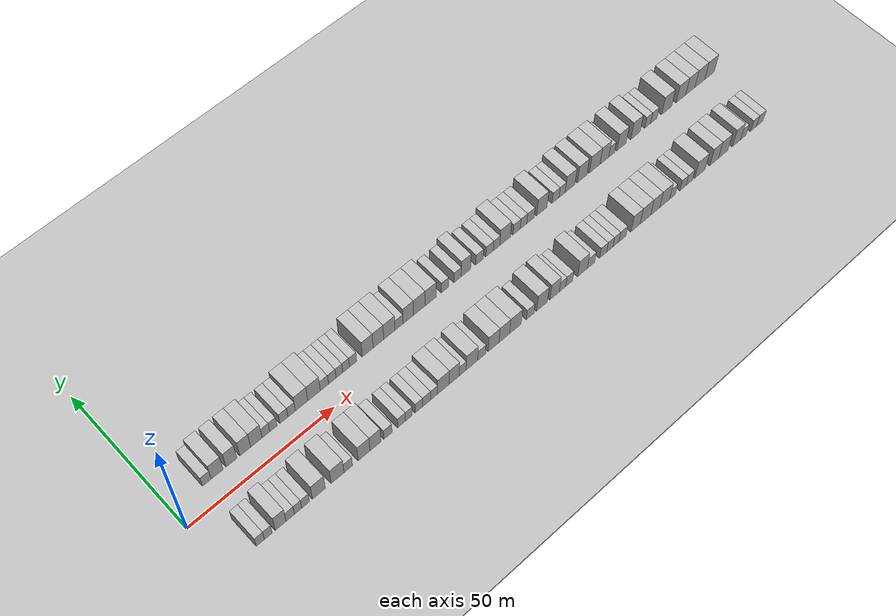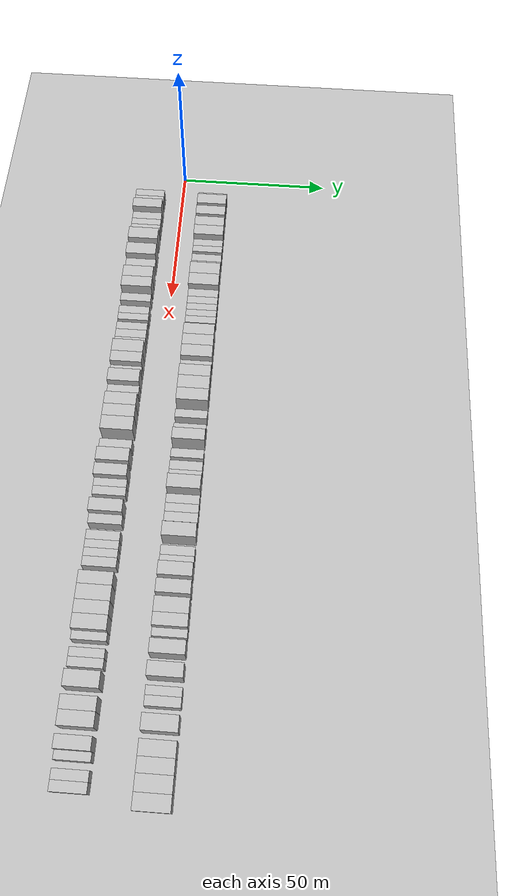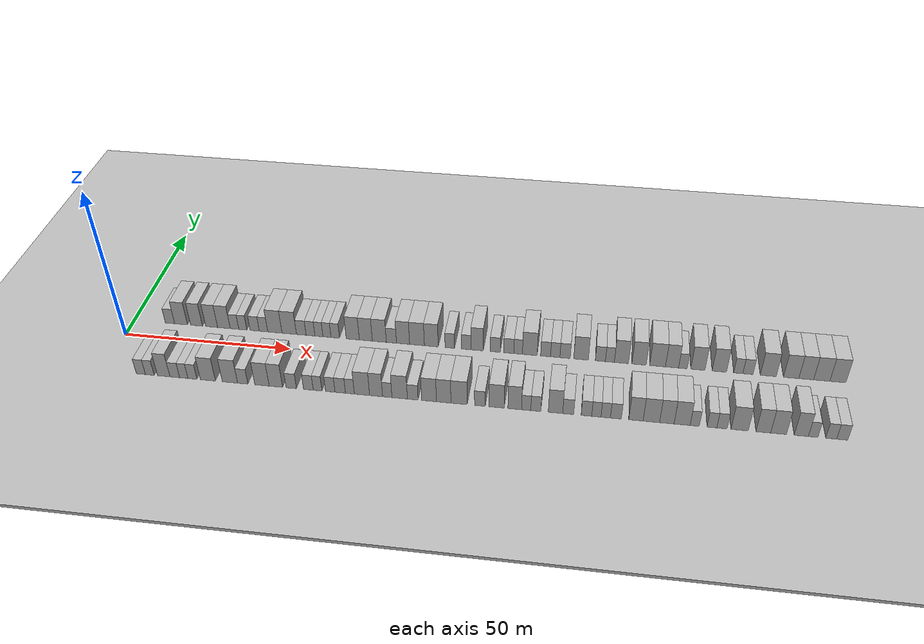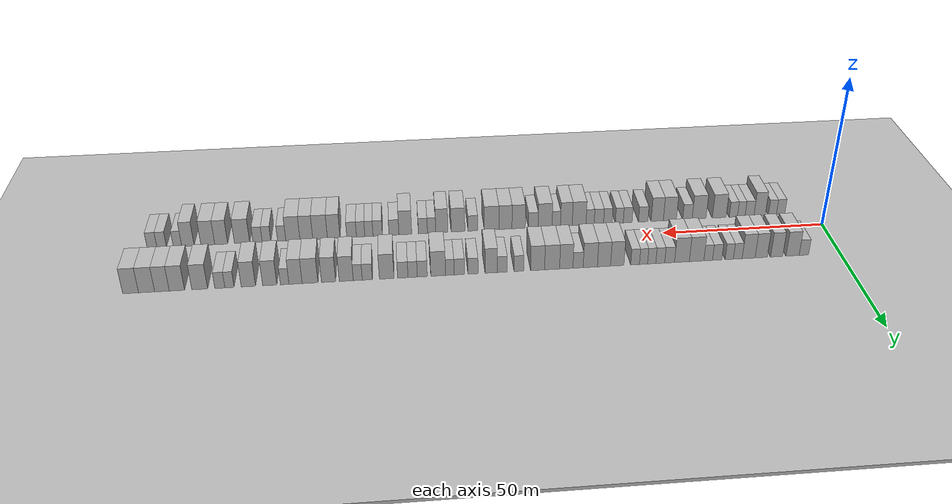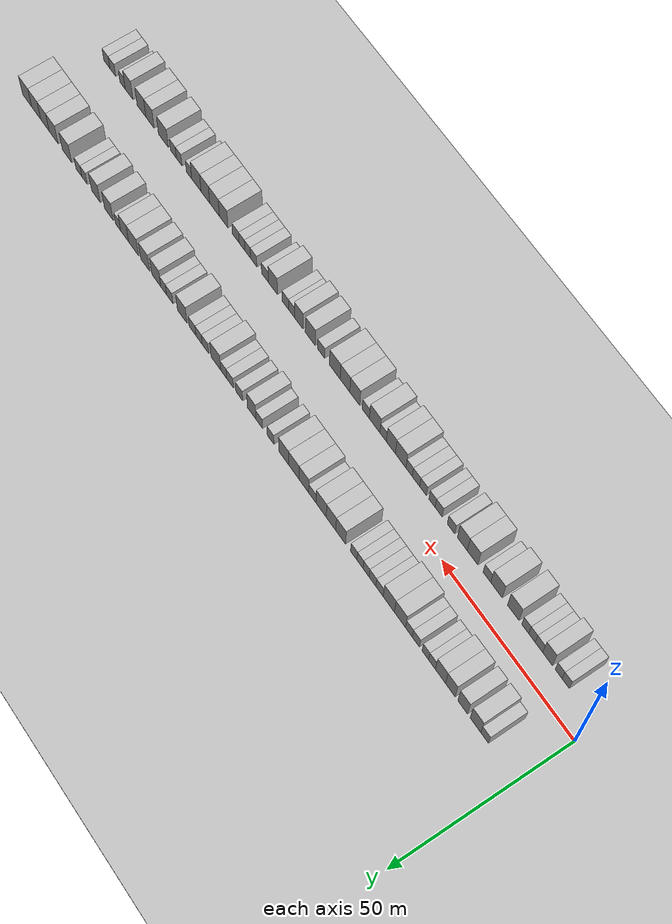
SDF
<?xml version="1.0" encoding="utf-8"?>

<sdf version="1.6">

   <world name="default">

      <gui fullscreen="0">

         <camera name="user_camera">

            <pose>-15 0 4.57585 0 0 0</pose>

            <view_controller>orbit</view_controller>

         </camera>

      </gui>

      <scene>

         <sky>

           <clouds>

             <speed>12</speed>

           </clouds>

         </sky>

         <ambient>0.4 0.4 0.4 1</ambient>

         <background>0.7 0.7 0.7 1</background>

         <shadows>1</shadows>

      </scene>

      <gravity>0 0 -9.8066</gravity>

      <magnetic_field>6e-06 2.3e-05 -4.2e-05</magnetic_field>

      <physics default="0" name="default_physics" type="ode">

         <ode>

            <solver>

               <type>quick</type>

               <iters>10</iters>

               <sor>1.0</sor>

               <use_dynamic_moi_rescaling>0</use_dynamic_moi_rescaling>

            </solver>

            <constraints>

               <cfm>0</cfm>

               <erp>0.2</erp>

               <contact_max_correcting_vel>100</contact_max_correcting_vel>

               <contact_surface_layer>0.001</contact_surface_layer>

            </constraints>

         </ode>

         <max_step_size>0.004</max_step_size>

         <real_time_factor>1</real_time_factor>

         <real_time_update_rate>250</real_time_update_rate>

      </physics>

      <light name="sun" type="directional">

         <cast_shadows>1</cast_shadows>

         <pose>0 0 10 0 0 0</pose>

         <diffuse>0.8 0.8 0.8 1</diffuse>

         <specular>0.2 0.2 0.2 1</specular>

         <attenuation>

            <range>1000</range>

            <constant>0.9</constant>

            <linear>0.01</linear>

            <quadratic>0.001</quadratic>

         </attenuation>

         <direction>-0.5 0.1 -0.9</direction>

      </light>

      <include>

         <name>ground_plane_1</name>

         <uri>model://HANNAS_ground_plane</uri>

         <pose>0 0 0  0 0 0</pose>

      </include>

      <include>

         <name>ground_plane_2</name>

         <uri>model://HANNAS_ground_plane</uri>

         <pose>100 0 0  0 0 0</pose>

      </include>

      <model name="building_1">

         <static>1</static>

         <pose frame="">11.4405 11.0000 0 0.000000 0.000000 1.570796</pose>

         <link name="link">

            <pose frame="">0 0 3.00 0 0 0</pose>

            <collision name="collision">

               <geometry>

                  <box>

                     <size>10.0000 2.8811 6.0000</size>

                  </box>

               </geometry>

               <max_contacts>10</max_contacts>

               <surface>

                  <contact>

                     <ode/>

                  </contact>

                  <bounce/>

                  <friction>

                     <torsional>

                        <ode/>

                     </torsional>

                     <ode/>

                  </friction>

               </surface>

            </collision>

            <visual name="visual">

               <cast_shadows>0</cast_shadows>

               <geometry>

                  <box>

                     <size>10.0000 2.8811 6.0000</size>

                  </box>

               </geometry>

               <material>

                  <script>

                     <uri>model://HANNAS_wall/materials/scripts</uri>

                     <uri>model://HANNAS_wall/materials/textures</uri>

                     <name>vrc/HANNAS_wall</name>

                  </script>

               </material>

            </visual>

            <self_collide>0</self_collide>

            <enable_wind>0</enable_wind>

            <kinematic>0</kinematic>

         </link>

      </model>

      <model name="building_2">

         <static>1</static>

         <pose frame="">14.8605 11.0000 0 0.000000 0.000000 1.570796</pose>

         <link name="link">

            <pose frame="">0 0 4.50 0 0 0</pose>

            <collision name="collision">

               <geometry>

                  <box>

                     <size>10.0000 3.9588 9.0000</size>

                  </box>

               </geometry>

               <max_contacts>10</max_contacts>

               <surface>

                  <contact>

                     <ode/>

                  </contact>

                  <bounce/>

                  <friction>

                     <torsional>

                        <ode/>

                     </torsional>

                     <ode/>

                  </friction>

               </surface>

            </collision>

            <visual name="visual">

               <cast_shadows>0</cast_shadows>

               <geometry>

                  <box>

                     <size>10.0000 3.9588 9.0000</size>

                  </box>

               </geometry>

               <material>

                  <script>

                     <uri>model://HANNAS_wall/materials/scripts</uri>

                     <uri>model://HANNAS_wall/materials/textures</uri>

                     <name>vrc/HANNAS_wall</name>

                  </script>

               </material>

            </visual>

            <self_collide>0</self_collide>

            <enable_wind>0</enable_wind>

            <kinematic>0</kinematic>

         </link>

      </model>

      <model name="building_3">

         <static>1</static>

         <pose frame="">19.6624 11.0000 0 0.000000 0.000000 1.570796</pose>

         <link name="link">

            <pose frame="">0 0 4.50 0 0 0</pose>

            <collision name="collision">

               <geometry>

                  <box>

                     <size>10.0000 3.6451 9.0000</size>

                  </box>

               </geometry>

               <max_contacts>10</max_contacts>

               <surface>

                  <contact>

                     <ode/>

                  </contact>

                  <bounce/>

                  <friction>

                     <torsional>

                        <ode/>

                     </torsional>

                     <ode/>

                  </friction>

               </surface>

            </collision>

            <visual name="visual">

               <cast_shadows>0</cast_shadows>

               <geometry>

                  <box>

                     <size>10.0000 3.6451 9.0000</size>

                  </box>

               </geometry>

               <material>

                  <script>

                     <uri>model://HANNAS_wall/materials/scripts</uri>

                     <uri>model://HANNAS_wall/materials/textures</uri>

                     <name>vrc/HANNAS_wall</name>

                  </script>

               </material>

            </visual>

            <self_collide>0</self_collide>

            <enable_wind>0</enable_wind>

            <kinematic>0</kinematic>

         </link>

      </model>

      <model name="building_4">

         <static>1</static>

         <pose frame="">24.3171 11.0000 0 0.000000 0.000000 1.570796</pose>

         <link name="link">

            <pose frame="">0 0 4.50 0 0 0</pose>

            <collision name="collision">

               <geometry>

                  <box>

                     <size>10.0000 3.6643 9.0000</size>

                  </box>

               </geometry>

               <max_contacts>10</max_contacts>

               <surface>

                  <contact>

                     <ode/>

                  </contact>

                  <bounce/>

                  <friction>

                     <torsional>

                        <ode/>

                     </torsional>

                     <ode/>

                  </friction>

               </surface>

            </collision>

            <visual name="visual">

               <cast_shadows>0</cast_shadows>

               <geometry>

                  <box>

                     <size>10.0000 3.6643 9.0000</size>

                  </box>

               </geometry>

               <material>

                  <script>

                     <uri>model://HANNAS_wall/materials/scripts</uri>

                     <uri>model://HANNAS_wall/materials/textures</uri>

                     <name>vrc/HANNAS_wall</name>

                  </script>

               </material>

            </visual>

            <self_collide>0</self_collide>

            <enable_wind>0</enable_wind>

            <kinematic>0</kinematic>

         </link>

      </model>

      <model name="building_5">

         <static>1</static>

         <pose frame="">28.0884 11.0000 0 0.000000 0.000000 1.570796</pose>

         <link name="link">

            <pose frame="">0 0 4.50 0 0 0</pose>

            <collision name="collision">

               <geometry>

                  <box>

                     <size>10.0000 3.8783 9.0000</size>

                  </box>

               </geometry>

               <max_contacts>10</max_contacts>

               <surface>

                  <contact>

                     <ode/>

                  </contact>

                  <bounce/>

                  <friction>

                     <torsional>

                        <ode/>

                     </torsional>

                     <ode/>

                  </friction>

               </surface>

            </collision>

            <visual name="visual">

               <cast_shadows>0</cast_shadows>

               <geometry>

                  <box>

                     <size>10.0000 3.8783 9.0000</size>

                  </box>

               </geometry>

               <material>

                  <script>

                     <uri>model://HANNAS_wall/materials/scripts</uri>

                     <uri>model://HANNAS_wall/materials/textures</uri>

                     <name>vrc/HANNAS_wall</name>

                  </script>

               </material>

            </visual>

            <self_collide>0</self_collide>

            <enable_wind>0</enable_wind>

            <kinematic>0</kinematic>

         </link>

      </model>

      <model name="building_6">

         <static>1</static>

         <pose frame="">31.3424 11.0000 0 0.000000 0.000000 1.570796</pose>

         <link name="link">

            <pose frame="">0 0 3.00 0 0 0</pose>

            <collision name="collision">

               <geometry>

                  <box>

                     <size>10.0000 2.6296 6.0000</size>

                  </box>

               </geometry>

               <max_contacts>10</max_contacts>

               <surface>

                  <contact>

                     <ode/>

                  </contact>

                  <bounce/>

                  <friction>

                     <torsional>

                        <ode/>

                     </torsional>

                     <ode/>

                  </friction>

               </surface>

            </collision>

            <visual name="visual">

               <cast_shadows>0</cast_shadows>

               <geometry>

                  <box>

                     <size>10.0000 2.6296 6.0000</size>

                  </box>

               </geometry>

               <material>

                  <script>

                     <uri>model://HANNAS_wall/materials/scripts</uri>

                     <uri>model://HANNAS_wall/materials/textures</uri>

                     <name>vrc/HANNAS_wall</name>

                  </script>

               </material>

            </visual>

            <self_collide>0</self_collide>

            <enable_wind>0</enable_wind>

            <kinematic>0</kinematic>

         </link>

      </model>

      <model name="building_7">

         <static>1</static>

         <pose frame="">33.8938 11.0000 0 0.000000 0.000000 1.570796</pose>

         <link name="link">

            <pose frame="">0 0 3.00 0 0 0</pose>

            <collision name="collision">

               <geometry>

                  <box>

                     <size>10.0000 2.4733 6.0000</size>

                  </box>

               </geometry>

               <max_contacts>10</max_contacts>

               <surface>

                  <contact>

                     <ode/>

                  </contact>

                  <bounce/>

                  <friction>

                     <torsional>

                        <ode/>

                     </torsional>

                     <ode/>

                  </friction>

               </surface>

            </collision>

            <visual name="visual">

               <cast_shadows>0</cast_shadows>

               <geometry>

                  <box>

                     <size>10.0000 2.4733 6.0000</size>

                  </box>

               </geometry>

               <material>

                  <script>

                     <uri>model://HANNAS_wall/materials/scripts</uri>

                     <uri>model://HANNAS_wall/materials/textures</uri>

                     <name>vrc/HANNAS_wall</name>

                  </script>

               </material>

            </visual>

            <self_collide>0</self_collide>

            <enable_wind>0</enable_wind>

            <kinematic>0</kinematic>

         </link>

      </model>

      <model name="building_8">

         <static>1</static>

         <pose frame="">37.5227 11.0000 0 0.000000 0.000000 1.570796</pose>

         <link name="link">

            <pose frame="">0 0 3.00 0 0 0</pose>

            <collision name="collision">

               <geometry>

                  <box>

                     <size>10.0000 2.7844 6.0000</size>

                  </box>

               </geometry>

               <max_contacts>10</max_contacts>

               <surface>

                  <contact>

                     <ode/>

                  </contact>

                  <bounce/>

                  <friction>

                     <torsional>

                        <ode/>

                     </torsional>

                     <ode/>

                  </friction>

               </surface>

            </collision>

            <visual name="visual">

               <cast_shadows>0</cast_shadows>

               <geometry>

                  <box>

                     <size>10.0000 2.7844 6.0000</size>

                  </box>

               </geometry>

               <material>

                  <script>

                     <uri>model://HANNAS_wall/materials/scripts</uri>

                     <uri>model://HANNAS_wall/materials/textures</uri>

                     <name>vrc/HANNAS_wall</name>

                  </script>

               </material>

            </visual>

            <self_collide>0</self_collide>

            <enable_wind>0</enable_wind>

            <kinematic>0</kinematic>

         </link>

      </model>

      <model name="building_9">

         <static>1</static>

         <pose frame="">40.1986 11.0000 0 0.000000 0.000000 1.570796</pose>

         <link name="link">

            <pose frame="">0 0 3.00 0 0 0</pose>

            <collision name="collision">

               <geometry>

                  <box>

                     <size>10.0000 2.5675 6.0000</size>

                  </box>

               </geometry>

               <max_contacts>10</max_contacts>

               <surface>

                  <contact>

                     <ode/>

                  </contact>

                  <bounce/>

                  <friction>

                     <torsional>

                        <ode/>

                     </torsional>

                     <ode/>

                  </friction>

               </surface>

            </collision>

            <visual name="visual">

               <cast_shadows>0</cast_shadows>

               <geometry>

                  <box>

                     <size>10.0000 2.5675 6.0000</size>

                  </box>

               </geometry>

               <material>

                  <script>

                     <uri>model://HANNAS_wall/materials/scripts</uri>

                     <uri>model://HANNAS_wall/materials/textures</uri>

                     <name>vrc/HANNAS_wall</name>

                  </script>

               </material>

            </visual>

            <self_collide>0</self_collide>

            <enable_wind>0</enable_wind>

            <kinematic>0</kinematic>

         </link>

      </model>

      <model name="building_10">

         <static>1</static>

         <pose frame="">43.6532 11.0000 0 0.000000 0.000000 1.570796</pose>

         <link name="link">

            <pose frame="">0 0 4.50 0 0 0</pose>

            <collision name="collision">

               <geometry>

                  <box>

                     <size>10.0000 4.3418 9.0000</size>

                  </box>

               </geometry>

               <max_contacts>10</max_contacts>

               <surface>

                  <contact>

                     <ode/>

                  </contact>

                  <bounce/>

                  <friction>

                     <torsional>

                        <ode/>

                     </torsional>

                     <ode/>

                  </friction>

               </surface>

            </collision>

            <visual name="visual">

               <cast_shadows>0</cast_shadows>

               <geometry>

                  <box>

                     <size>10.0000 4.3418 9.0000</size>

                  </box>

               </geometry>

               <material>

                  <script>

                     <uri>model://HANNAS_wall/materials/scripts</uri>

                     <uri>model://HANNAS_wall/materials/textures</uri>

                     <name>vrc/HANNAS_wall</name>

                  </script>

               </material>

            </visual>

            <self_collide>0</self_collide>

            <enable_wind>0</enable_wind>

            <kinematic>0</kinematic>

         </link>

      </model>

      <model name="building_11">

         <static>1</static>

         <pose frame="">48.0235 11.0000 0 0.000000 0.000000 1.570796</pose>

         <link name="link">

            <pose frame="">0 0 4.50 0 0 0</pose>

            <collision name="collision">

               <geometry>

                  <box>

                     <size>10.0000 4.3988 9.0000</size>

                  </box>

               </geometry>

               <max_contacts>10</max_contacts>

               <surface>

                  <contact>

                     <ode/>

                  </contact>

                  <bounce/>

                  <friction>

                     <torsional>

                        <ode/>

                     </torsional>

                     <ode/>

                  </friction>

               </surface>

            </collision>

            <visual name="visual">

               <cast_shadows>0</cast_shadows>

               <geometry>

                  <box>

                     <size>10.0000 4.3988 9.0000</size>

                  </box>

               </geometry>

               <material>

                  <script>

                     <uri>model://HANNAS_wall/materials/scripts</uri>

                     <uri>model://HANNAS_wall/materials/textures</uri>

                     <name>vrc/HANNAS_wall</name>

                  </script>

               </material>

            </visual>

            <self_collide>0</self_collide>

            <enable_wind>0</enable_wind>

            <kinematic>0</kinematic>

         </link>

      </model>

      <model name="building_12">

         <static>1</static>

         <pose frame="">51.6736 11.0000 0 0.000000 0.000000 1.570796</pose>

         <link name="link">

            <pose frame="">0 0 3.00 0 0 0</pose>

            <collision name="collision">

               <geometry>

                  <box>

                     <size>10.0000 2.9014 6.0000</size>

                  </box>

               </geometry>

               <max_contacts>10</max_contacts>

               <surface>

                  <contact>

                     <ode/>

                  </contact>

                  <bounce/>

                  <friction>

                     <torsional>

                        <ode/>

                     </torsional>

                     <ode/>

                  </friction>

               </surface>

            </collision>

            <visual name="visual">

               <cast_shadows>0</cast_shadows>

               <geometry>

                  <box>

                     <size>10.0000 2.9014 6.0000</size>

                  </box>

               </geometry>

               <material>

                  <script>

                     <uri>model://HANNAS_wall/materials/scripts</uri>

                     <uri>model://HANNAS_wall/materials/textures</uri>

                     <name>vrc/HANNAS_wall</name>

                  </script>

               </material>

            </visual>

            <self_collide>0</self_collide>

            <enable_wind>0</enable_wind>

            <kinematic>0</kinematic>

         </link>

      </model>

      <model name="building_13">

         <static>1</static>

         <pose frame="">54.4530 11.0000 0 0.000000 0.000000 1.570796</pose>

         <link name="link">

            <pose frame="">0 0 3.00 0 0 0</pose>

            <collision name="collision">

               <geometry>

                  <box>

                     <size>10.0000 2.6574 6.0000</size>

                  </box>

               </geometry>

               <max_contacts>10</max_contacts>

               <surface>

                  <contact>

                     <ode/>

                  </contact>

                  <bounce/>

                  <friction>

                     <torsional>

                        <ode/>

                     </torsional>

                     <ode/>

                  </friction>

               </surface>

            </collision>

            <visual name="visual">

               <cast_shadows>0</cast_shadows>

               <geometry>

                  <box>

                     <size>10.0000 2.6574 6.0000</size>

                  </box>

               </geometry>

               <material>

                  <script>

                     <uri>model://HANNAS_wall/materials/scripts</uri>

                     <uri>model://HANNAS_wall/materials/textures</uri>

                     <name>vrc/HANNAS_wall</name>

                  </script>

               </material>

            </visual>

            <self_collide>0</self_collide>

            <enable_wind>0</enable_wind>

            <kinematic>0</kinematic>

         </link>

      </model>

      <model name="building_14">

         <static>1</static>

         <pose frame="">56.9940 11.0000 0 0.000000 0.000000 1.570796</pose>

         <link name="link">

            <pose frame="">0 0 3.00 0 0 0</pose>

            <collision name="collision">

               <geometry>

                  <box>

                     <size>10.0000 2.4246 6.0000</size>

                  </box>

               </geometry>

               <max_contacts>10</max_contacts>

               <surface>

                  <contact>

                     <ode/>

                  </contact>

                  <bounce/>

                  <friction>

                     <torsional>

                        <ode/>

                     </torsional>

                     <ode/>

                  </friction>

               </surface>

            </collision>

            <visual name="visual">

               <cast_shadows>0</cast_shadows>

               <geometry>

                  <box>

                     <size>10.0000 2.4246 6.0000</size>

                  </box>

               </geometry>

               <material>

                  <script>

                     <uri>model://HANNAS_wall/materials/scripts</uri>

                     <uri>model://HANNAS_wall/materials/textures</uri>

                     <name>vrc/HANNAS_wall</name>

                  </script>

               </material>

            </visual>

            <self_collide>0</self_collide>

            <enable_wind>0</enable_wind>

            <kinematic>0</kinematic>

         </link>

      </model>

      <model name="building_15">

         <static>1</static>

         <pose frame="">59.4090 11.0000 0 0.000000 0.000000 1.570796</pose>

         <link name="link">

            <pose frame="">0 0 3.00 0 0 0</pose>

            <collision name="collision">

               <geometry>

                  <box>

                     <size>10.0000 2.4054 6.0000</size>

                  </box>

               </geometry>

               <max_contacts>10</max_contacts>

               <surface>

                  <contact>

                     <ode/>

                  </contact>

                  <bounce/>

                  <friction>

                     <torsional>

                        <ode/>

                     </torsional>

                     <ode/>

                  </friction>

               </surface>

            </collision>

            <visual name="visual">

               <cast_shadows>0</cast_shadows>

               <geometry>

                  <box>

                     <size>10.0000 2.4054 6.0000</size>

                  </box>

               </geometry>

               <material>

                  <script>

                     <uri>model://HANNAS_wall/materials/scripts</uri>

                     <uri>model://HANNAS_wall/materials/textures</uri>

                     <name>vrc/HANNAS_wall</name>

                  </script>

               </material>

            </visual>

            <self_collide>0</self_collide>

            <enable_wind>0</enable_wind>

            <kinematic>0</kinematic>

         </link>

      </model>

      <model name="building_16">

         <static>1</static>

         <pose frame="">61.9006 11.0000 0 0.000000 0.000000 1.570796</pose>

         <link name="link">

            <pose frame="">0 0 3.00 0 0 0</pose>

            <collision name="collision">

               <geometry>

                  <box>

                     <size>10.0000 2.5778 6.0000</size>

                  </box>

               </geometry>

               <max_contacts>10</max_contacts>

               <surface>

                  <contact>

                     <ode/>

                  </contact>

                  <bounce/>

                  <friction>

                     <torsional>

                        <ode/>

                     </torsional>

                     <ode/>

                  </friction>

               </surface>

            </collision>

            <visual name="visual">

               <cast_shadows>0</cast_shadows>

               <geometry>

                  <box>

                     <size>10.0000 2.5778 6.0000</size>

                  </box>

               </geometry>

               <material>

                  <script>

                     <uri>model://HANNAS_wall/materials/scripts</uri>

                     <uri>model://HANNAS_wall/materials/textures</uri>

                     <name>vrc/HANNAS_wall</name>

                  </script>

               </material>

            </visual>

            <self_collide>0</self_collide>

            <enable_wind>0</enable_wind>

            <kinematic>0</kinematic>

         </link>

      </model>

      <model name="building_17">

         <static>1</static>

         <pose frame="">67.1540 11.0000 0 0.000000 0.000000 1.570796</pose>

         <link name="link">

            <pose frame="">0 0 4.50 0 0 0</pose>

            <collision name="collision">

               <geometry>

                  <box>

                     <size>10.0000 3.9290 9.0000</size>

                  </box>

               </geometry>

               <max_contacts>10</max_contacts>

               <surface>

                  <contact>

                     <ode/>

                  </contact>

                  <bounce/>

                  <friction>

                     <torsional>

                        <ode/>

                     </torsional>

                     <ode/>

                  </friction>

               </surface>

            </collision>

            <visual name="visual">

               <cast_shadows>0</cast_shadows>

               <geometry>

                  <box>

                     <size>10.0000 3.9290 9.0000</size>

                  </box>

               </geometry>

               <material>

                  <script>

                     <uri>model://HANNAS_wall/materials/scripts</uri>

                     <uri>model://HANNAS_wall/materials/textures</uri>

                     <name>vrc/HANNAS_wall</name>

                  </script>

               </material>

            </visual>

            <self_collide>0</self_collide>

            <enable_wind>0</enable_wind>

            <kinematic>0</kinematic>

         </link>

      </model>

      <model name="building_18">

         <static>1</static>

         <pose frame="">71.0563 11.0000 0 0.000000 0.000000 1.570796</pose>

         <link name="link">

            <pose frame="">0 0 4.50 0 0 0</pose>

            <collision name="collision">

               <geometry>

                  <box>

                     <size>10.0000 3.8756 9.0000</size>

                  </box>

               </geometry>

               <max_contacts>10</max_contacts>

               <surface>

                  <contact>

                     <ode/>

                  </contact>

                  <bounce/>

                  <friction>

                     <torsional>

                        <ode/>

                     </torsional>

                     <ode/>

                  </friction>

               </surface>

            </collision>

            <visual name="visual">

               <cast_shadows>0</cast_shadows>

               <geometry>

                  <box>

                     <size>10.0000 3.8756 9.0000</size>

                  </box>

               </geometry>

               <material>

                  <script>

                     <uri>model://HANNAS_wall/materials/scripts</uri>

                     <uri>model://HANNAS_wall/materials/textures</uri>

                     <name>vrc/HANNAS_wall</name>

                  </script>

               </material>

            </visual>

            <self_collide>0</self_collide>

            <enable_wind>0</enable_wind>

            <kinematic>0</kinematic>

         </link>

      </model>

      <model name="building_19">

         <static>1</static>

         <pose frame="">75.0803 11.0000 0 0.000000 0.000000 1.570796</pose>

         <link name="link">

            <pose frame="">0 0 4.50 0 0 0</pose>

            <collision name="collision">

               <geometry>

                  <box>

                     <size>10.0000 4.1723 9.0000</size>

                  </box>

               </geometry>

               <max_contacts>10</max_contacts>

               <surface>

                  <contact>

                     <ode/>

                  </contact>

                  <bounce/>

                  <friction>

                     <torsional>

                        <ode/>

                     </torsional>

                     <ode/>

                  </friction>

               </surface>

            </collision>

            <visual name="visual">

               <cast_shadows>0</cast_shadows>

               <geometry>

                  <box>

                     <size>10.0000 4.1723 9.0000</size>

                  </box>

               </geometry>

               <material>

                  <script>

                     <uri>model://HANNAS_wall/materials/scripts</uri>

                     <uri>model://HANNAS_wall/materials/textures</uri>

                     <name>vrc/HANNAS_wall</name>

                  </script>

               </material>

            </visual>

            <self_collide>0</self_collide>

            <enable_wind>0</enable_wind>

            <kinematic>0</kinematic>

         </link>

      </model>

      <model name="building_20">

         <static>1</static>

         <pose frame="">78.6641 11.0000 0 0.000000 0.000000 1.570796</pose>

         <link name="link">

            <pose frame="">0 0 3.00 0 0 0</pose>

            <collision name="collision">

               <geometry>

                  <box>

                     <size>10.0000 2.9954 6.0000</size>

                  </box>

               </geometry>

               <max_contacts>10</max_contacts>

               <surface>

                  <contact>

                     <ode/>

                  </contact>

                  <bounce/>

                  <friction>

                     <torsional>

                        <ode/>

                     </torsional>

                     <ode/>

                  </friction>

               </surface>

            </collision>

            <visual name="visual">

               <cast_shadows>0</cast_shadows>

               <geometry>

                  <box>

                     <size>10.0000 2.9954 6.0000</size>

                  </box>

               </geometry>

               <material>

                  <script>

                     <uri>model://HANNAS_wall/materials/scripts</uri>

                     <uri>model://HANNAS_wall/materials/textures</uri>

                     <name>vrc/HANNAS_wall</name>

                  </script>

               </material>

            </visual>

            <self_collide>0</self_collide>

            <enable_wind>0</enable_wind>

            <kinematic>0</kinematic>

         </link>

      </model>

      <model name="building_21">

         <static>1</static>

         <pose frame="">82.1052 11.0000 0 0.000000 0.000000 1.570796</pose>

         <link name="link">

            <pose frame="">0 0 4.50 0 0 0</pose>

            <collision name="collision">

               <geometry>

                  <box>

                     <size>10.0000 3.8867 9.0000</size>

                  </box>

               </geometry>

               <max_contacts>10</max_contacts>

               <surface>

                  <contact>

                     <ode/>

                  </contact>

                  <bounce/>

                  <friction>

                     <torsional>

                        <ode/>

                     </torsional>

                     <ode/>

                  </friction>

               </surface>

            </collision>

            <visual name="visual">

               <cast_shadows>0</cast_shadows>

               <geometry>

                  <box>

                     <size>10.0000 3.8867 9.0000</size>

                  </box>

               </geometry>

               <material>

                  <script>

                     <uri>model://HANNAS_wall/materials/scripts</uri>

                     <uri>model://HANNAS_wall/materials/textures</uri>

                     <name>vrc/HANNAS_wall</name>

                  </script>

               </material>

            </visual>

            <self_collide>0</self_collide>

            <enable_wind>0</enable_wind>

            <kinematic>0</kinematic>

         </link>

      </model>

      <model name="building_22">

         <static>1</static>

         <pose frame="">86.2344 11.0000 0 0.000000 0.000000 1.570796</pose>

         <link name="link">

            <pose frame="">0 0 4.50 0 0 0</pose>

            <collision name="collision">

               <geometry>

                  <box>

                     <size>10.0000 4.3718 9.0000</size>

                  </box>

               </geometry>

               <max_contacts>10</max_contacts>

               <surface>

                  <contact>

                     <ode/>

                  </contact>

                  <bounce/>

                  <friction>

                     <torsional>

                        <ode/>

                     </torsional>

                     <ode/>

                  </friction>

               </surface>

            </collision>

            <visual name="visual">

               <cast_shadows>0</cast_shadows>

               <geometry>

                  <box>

                     <size>10.0000 4.3718 9.0000</size>

                  </box>

               </geometry>

               <material>

                  <script>

                     <uri>model://HANNAS_wall/materials/scripts</uri>

                     <uri>model://HANNAS_wall/materials/textures</uri>

                     <name>vrc/HANNAS_wall</name>

                  </script>

               </material>

            </visual>

            <self_collide>0</self_collide>

            <enable_wind>0</enable_wind>

            <kinematic>0</kinematic>

         </link>

      </model>

      <model name="building_23">

         <static>1</static>

         <pose frame="">90.4576 11.0000 0 0.000000 0.000000 1.570796</pose>

         <link name="link">

            <pose frame="">0 0 4.50 0 0 0</pose>

            <collision name="collision">

               <geometry>

                  <box>

                     <size>10.0000 4.0745 9.0000</size>

                  </box>

               </geometry>

               <max_contacts>10</max_contacts>

               <surface>

                  <contact>

                     <ode/>

                  </contact>

                  <bounce/>

                  <friction>

                     <torsional>

                        <ode/>

                     </torsional>

                     <ode/>

                  </friction>

               </surface>

            </collision>

            <visual name="visual">

               <cast_shadows>0</cast_shadows>

               <geometry>

                  <box>

                     <size>10.0000 4.0745 9.0000</size>

                  </box>

               </geometry>

               <material>

                  <script>

                     <uri>model://HANNAS_wall/materials/scripts</uri>

                     <uri>model://HANNAS_wall/materials/textures</uri>

                     <name>vrc/HANNAS_wall</name>

                  </script>

               </material>

            </visual>

            <self_collide>0</self_collide>

            <enable_wind>0</enable_wind>

            <kinematic>0</kinematic>

         </link>

      </model>

      <model name="building_24">

         <static>1</static>

         <pose frame="">95.8863 11.0000 0 0.000000 0.000000 1.570796</pose>

         <link name="link">

            <pose frame="">0 0 3.00 0 0 0</pose>

            <collision name="collision">

               <geometry>

                  <box>

                     <size>10.0000 2.7829 6.0000</size>

                  </box>

               </geometry>

               <max_contacts>10</max_contacts>

               <surface>

                  <contact>

                     <ode/>

                  </contact>

                  <bounce/>

                  <friction>

                     <torsional>

                        <ode/>

                     </torsional>

                     <ode/>

                  </friction>

               </surface>

            </collision>

            <visual name="visual">

               <cast_shadows>0</cast_shadows>

               <geometry>

                  <box>

                     <size>10.0000 2.7829 6.0000</size>

                  </box>

               </geometry>

               <material>

                  <script>

                     <uri>model://HANNAS_wall/materials/scripts</uri>

                     <uri>model://HANNAS_wall/materials/textures</uri>

                     <name>vrc/HANNAS_wall</name>

                  </script>

               </material>

            </visual>

            <self_collide>0</self_collide>

            <enable_wind>0</enable_wind>

            <kinematic>0</kinematic>

         </link>

      </model>

      <model name="building_25">

         <static>1</static>

         <pose frame="">100.6699 11.0000 0 0.000000 0.000000 1.570796</pose>

         <link name="link">

            <pose frame="">0 0 3.00 0 0 0</pose>

            <collision name="collision">

               <geometry>

                  <box>

                     <size>10.0000 2.7842 6.0000</size>

                  </box>

               </geometry>

               <max_contacts>10</max_contacts>

               <surface>

                  <contact>

                     <ode/>

                  </contact>

                  <bounce/>

                  <friction>

                     <torsional>

                        <ode/>

                     </torsional>

                     <ode/>

                  </friction>

               </surface>

            </collision>

            <visual name="visual">

               <cast_shadows>0</cast_shadows>

               <geometry>

                  <box>

                     <size>10.0000 2.7842 6.0000</size>

                  </box>

               </geometry>

               <material>

                  <script>

                     <uri>model://HANNAS_wall/materials/scripts</uri>

                     <uri>model://HANNAS_wall/materials/textures</uri>

                     <name>vrc/HANNAS_wall</name>

                  </script>

               </material>

            </visual>

            <self_collide>0</self_collide>

            <enable_wind>0</enable_wind>

            <kinematic>0</kinematic>

         </link>

      </model>

      <model name="building_26">

         <static>1</static>

         <pose frame="">103.8715 11.0000 0 0.000000 0.000000 1.570796</pose>

         <link name="link">

            <pose frame="">0 0 4.50 0 0 0</pose>

            <collision name="collision">

               <geometry>

                  <box>

                     <size>10.0000 3.6191 9.0000</size>

                  </box>

               </geometry>

               <max_contacts>10</max_contacts>

               <surface>

                  <contact>

                     <ode/>

                  </contact>

                  <bounce/>

                  <friction>

                     <torsional>

                        <ode/>

                     </torsional>

                     <ode/>

                  </friction>

               </surface>

            </collision>

            <visual name="visual">

               <cast_shadows>0</cast_shadows>

               <geometry>

                  <box>

                     <size>10.0000 3.6191 9.0000</size>

                  </box>

               </geometry>

               <material>

                  <script>

                     <uri>model://HANNAS_wall/materials/scripts</uri>

                     <uri>model://HANNAS_wall/materials/textures</uri>

                     <name>vrc/HANNAS_wall</name>

                  </script>

               </material>

            </visual>

            <self_collide>0</self_collide>

            <enable_wind>0</enable_wind>

            <kinematic>0</kinematic>

         </link>

      </model>

      <model name="building_27">

         <static>1</static>

         <pose frame="">109.1415 11.0000 0 0.000000 0.000000 1.570796</pose>

         <link name="link">

            <pose frame="">0 0 3.00 0 0 0</pose>

            <collision name="collision">

               <geometry>

                  <box>

                     <size>10.0000 2.9207 6.0000</size>

                  </box>

               </geometry>

               <max_contacts>10</max_contacts>

               <surface>

                  <contact>

                     <ode/>

                  </contact>

                  <bounce/>

                  <friction>

                     <torsional>

                        <ode/>

                     </torsional>

                     <ode/>

                  </friction>

               </surface>

            </collision>

            <visual name="visual">

               <cast_shadows>0</cast_shadows>

               <geometry>

                  <box>

                     <size>10.0000 2.9207 6.0000</size>

                  </box>

               </geometry>

               <material>

                  <script>

                     <uri>model://HANNAS_wall/materials/scripts</uri>

                     <uri>model://HANNAS_wall/materials/textures</uri>

                     <name>vrc/HANNAS_wall</name>

                  </script>

               </material>

            </visual>

            <self_collide>0</self_collide>

            <enable_wind>0</enable_wind>

            <kinematic>0</kinematic>

         </link>

      </model>

      <model name="building_28">

         <static>1</static>

         <pose frame="">113.0786 11.0000 0 0.000000 0.000000 1.570796</pose>

         <link name="link">

            <pose frame="">0 0 3.00 0 0 0</pose>

            <collision name="collision">

               <geometry>

                  <box>

                     <size>10.0000 2.9536 6.0000</size>

                  </box>

               </geometry>

               <max_contacts>10</max_contacts>

               <surface>

                  <contact>

                     <ode/>

                  </contact>

                  <bounce/>

                  <friction>

                     <torsional>

                        <ode/>

                     </torsional>

                     <ode/>

                  </friction>

               </surface>

            </collision>

            <visual name="visual">

               <cast_shadows>0</cast_shadows>

               <geometry>

                  <box>

                     <size>10.0000 2.9536 6.0000</size>

                  </box>

               </geometry>

               <material>

                  <script>

                     <uri>model://HANNAS_wall/materials/scripts</uri>

                     <uri>model://HANNAS_wall/materials/textures</uri>

                     <name>vrc/HANNAS_wall</name>

                  </script>

               </material>

            </visual>

            <self_collide>0</self_collide>

            <enable_wind>0</enable_wind>

            <kinematic>0</kinematic>

         </link>

      </model>

      <model name="building_29">

         <static>1</static>

         <pose frame="">115.7921 11.0000 0 0.000000 0.000000 1.570796</pose>

         <link name="link">

            <pose frame="">0 0 3.00 0 0 0</pose>

            <collision name="collision">

               <geometry>

                  <box>

                     <size>10.0000 2.4733 6.0000</size>

                  </box>

               </geometry>

               <max_contacts>10</max_contacts>

               <surface>

                  <contact>

                     <ode/>

                  </contact>

                  <bounce/>

                  <friction>

                     <torsional>

                        <ode/>

                     </torsional>

                     <ode/>

                  </friction>

               </surface>

            </collision>

            <visual name="visual">

               <cast_shadows>0</cast_shadows>

               <geometry>

                  <box>

                     <size>10.0000 2.4733 6.0000</size>

                  </box>

               </geometry>

               <material>

                  <script>

                     <uri>model://HANNAS_wall/materials/scripts</uri>

                     <uri>model://HANNAS_wall/materials/textures</uri>

                     <name>vrc/HANNAS_wall</name>

                  </script>

               </material>

            </visual>

            <self_collide>0</self_collide>

            <enable_wind>0</enable_wind>

            <kinematic>0</kinematic>

         </link>

      </model>

      <model name="building_30">

         <static>1</static>

         <pose frame="">119.1500 11.0000 0 0.000000 0.000000 1.570796</pose>

         <link name="link">

            <pose frame="">0 0 4.50 0 0 0</pose>

            <collision name="collision">

               <geometry>

                  <box>

                     <size>10.0000 4.2424 9.0000</size>

                  </box>

               </geometry>

               <max_contacts>10</max_contacts>

               <surface>

                  <contact>

                     <ode/>

                  </contact>

                  <bounce/>

                  <friction>

                     <torsional>

                        <ode/>

                     </torsional>

                     <ode/>

                  </friction>

               </surface>

            </collision>

            <visual name="visual">

               <cast_shadows>0</cast_shadows>

               <geometry>

                  <box>

                     <size>10.0000 4.2424 9.0000</size>

                  </box>

               </geometry>

               <material>

                  <script>

                     <uri>model://HANNAS_wall/materials/scripts</uri>

                     <uri>model://HANNAS_wall/materials/textures</uri>

                     <name>vrc/HANNAS_wall</name>

                  </script>

               </material>

            </visual>

            <self_collide>0</self_collide>

            <enable_wind>0</enable_wind>

            <kinematic>0</kinematic>

         </link>

      </model>

      <model name="building_31">

         <static>1</static>

         <pose frame="">123.6941 11.0000 0 0.000000 0.000000 1.570796</pose>

         <link name="link">

            <pose frame="">0 0 3.00 0 0 0</pose>

            <collision name="collision">

               <geometry>

                  <box>

                     <size>10.0000 2.8459 6.0000</size>

                  </box>

               </geometry>

               <max_contacts>10</max_contacts>

               <surface>

                  <contact>

                     <ode/>

                  </contact>

                  <bounce/>

                  <friction>

                     <torsional>

                        <ode/>

                     </torsional>

                     <ode/>

                  </friction>

               </surface>

            </collision>

            <visual name="visual">

               <cast_shadows>0</cast_shadows>

               <geometry>

                  <box>

                     <size>10.0000 2.8459 6.0000</size>

                  </box>

               </geometry>

               <material>

                  <script>

                     <uri>model://HANNAS_wall/materials/scripts</uri>

                     <uri>model://HANNAS_wall/materials/textures</uri>

                     <name>vrc/HANNAS_wall</name>

                  </script>

               </material>

            </visual>

            <self_collide>0</self_collide>

            <enable_wind>0</enable_wind>

            <kinematic>0</kinematic>

         </link>

      </model>

      <model name="building_32">

         <static>1</static>

         <pose frame="">126.4587 11.0000 0 0.000000 0.000000 1.570796</pose>

         <link name="link">

            <pose frame="">0 0 3.00 0 0 0</pose>

            <collision name="collision">

               <geometry>

                  <box>

                     <size>10.0000 2.6832 6.0000</size>

                  </box>

               </geometry>

               <max_contacts>10</max_contacts>

               <surface>

                  <contact>

                     <ode/>

                  </contact>

                  <bounce/>

                  <friction>

                     <torsional>

                        <ode/>

                     </torsional>

                     <ode/>

                  </friction>

               </surface>

            </collision>

            <visual name="visual">

               <cast_shadows>0</cast_shadows>

               <geometry>

                  <box>

                     <size>10.0000 2.6832 6.0000</size>

                  </box>

               </geometry>

               <material>

                  <script>

                     <uri>model://HANNAS_wall/materials/scripts</uri>

                     <uri>model://HANNAS_wall/materials/textures</uri>

                     <name>vrc/HANNAS_wall</name>

                  </script>

               </material>

            </visual>

            <self_collide>0</self_collide>

            <enable_wind>0</enable_wind>

            <kinematic>0</kinematic>

         </link>

      </model>

      <model name="building_33">

         <static>1</static>

         <pose frame="">129.2818 11.0000 0 0.000000 0.000000 1.570796</pose>

         <link name="link">

            <pose frame="">0 0 3.00 0 0 0</pose>

            <collision name="collision">

               <geometry>

                  <box>

                     <size>10.0000 2.9631 6.0000</size>

                  </box>

               </geometry>

               <max_contacts>10</max_contacts>

               <surface>

                  <contact>

                     <ode/>

                  </contact>

                  <bounce/>

                  <friction>

                     <torsional>

                        <ode/>

                     </torsional>

                     <ode/>

                  </friction>

               </surface>

            </collision>

            <visual name="visual">

               <cast_shadows>0</cast_shadows>

               <geometry>

                  <box>

                     <size>10.0000 2.9631 6.0000</size>

                  </box>

               </geometry>

               <material>

                  <script>

                     <uri>model://HANNAS_wall/materials/scripts</uri>

                     <uri>model://HANNAS_wall/materials/textures</uri>

                     <name>vrc/HANNAS_wall</name>

                  </script>

               </material>

            </visual>

            <self_collide>0</self_collide>

            <enable_wind>0</enable_wind>

            <kinematic>0</kinematic>

         </link>

      </model>

      <model name="building_34">

         <static>1</static>

         <pose frame="">133.8488 11.0000 0 0.000000 0.000000 1.570796</pose>

         <link name="link">

            <pose frame="">0 0 4.50 0 0 0</pose>

            <collision name="collision">

               <geometry>

                  <box>

                     <size>10.0000 4.1709 9.0000</size>

                  </box>

               </geometry>

               <max_contacts>10</max_contacts>

               <surface>

                  <contact>

                     <ode/>

                  </contact>

                  <bounce/>

                  <friction>

                     <torsional>

                        <ode/>

                     </torsional>

                     <ode/>

                  </friction>

               </surface>

            </collision>

            <visual name="visual">

               <cast_shadows>0</cast_shadows>

               <geometry>

                  <box>

                     <size>10.0000 4.1709 9.0000</size>

                  </box>

               </geometry>

               <material>

                  <script>

                     <uri>model://HANNAS_wall/materials/scripts</uri>

                     <uri>model://HANNAS_wall/materials/textures</uri>

                     <name>vrc/HANNAS_wall</name>

                  </script>

               </material>

            </visual>

            <self_collide>0</self_collide>

            <enable_wind>0</enable_wind>

            <kinematic>0</kinematic>

         </link>

      </model>

      <model name="building_35">

         <static>1</static>

         <pose frame="">139.3656 11.0000 0 0.000000 0.000000 1.570796</pose>

         <link name="link">

            <pose frame="">0 0 3.00 0 0 0</pose>

            <collision name="collision">

               <geometry>

                  <box>

                     <size>10.0000 2.8626 6.0000</size>

                  </box>

               </geometry>

               <max_contacts>10</max_contacts>

               <surface>

                  <contact>

                     <ode/>

                  </contact>

                  <bounce/>

                  <friction>

                     <torsional>

                        <ode/>

                     </torsional>

                     <ode/>

                  </friction>

               </surface>

            </collision>

            <visual name="visual">

               <cast_shadows>0</cast_shadows>

               <geometry>

                  <box>

                     <size>10.0000 2.8626 6.0000</size>

                  </box>

               </geometry>

               <material>

                  <script>

                     <uri>model://HANNAS_wall/materials/scripts</uri>

                     <uri>model://HANNAS_wall/materials/textures</uri>

                     <name>vrc/HANNAS_wall</name>

                  </script>

               </material>

            </visual>

            <self_collide>0</self_collide>

            <enable_wind>0</enable_wind>

            <kinematic>0</kinematic>

         </link>

      </model>

      <model name="building_36">

         <static>1</static>

         <pose frame="">142.0650 11.0000 0 0.000000 0.000000 1.570796</pose>

         <link name="link">

            <pose frame="">0 0 3.00 0 0 0</pose>

            <collision name="collision">

               <geometry>

                  <box>

                     <size>10.0000 2.5362 6.0000</size>

                  </box>

               </geometry>

               <max_contacts>10</max_contacts>

               <surface>

                  <contact>

                     <ode/>

                  </contact>

                  <bounce/>

                  <friction>

                     <torsional>

                        <ode/>

                     </torsional>

                     <ode/>

                  </friction>

               </surface>

            </collision>

            <visual name="visual">

               <cast_shadows>0</cast_shadows>

               <geometry>

                  <box>

                     <size>10.0000 2.5362 6.0000</size>

                  </box>

               </geometry>

               <material>

                  <script>

                     <uri>model://HANNAS_wall/materials/scripts</uri>

                     <uri>model://HANNAS_wall/materials/textures</uri>

                     <name>vrc/HANNAS_wall</name>

                  </script>

               </material>

            </visual>

            <self_collide>0</self_collide>

            <enable_wind>0</enable_wind>

            <kinematic>0</kinematic>

         </link>

      </model>

      <model name="building_37">

         <static>1</static>

         <pose frame="">145.3249 11.0000 0 0.000000 0.000000 1.570796</pose>

         <link name="link">

            <pose frame="">0 0 4.50 0 0 0</pose>

            <collision name="collision">

               <geometry>

                  <box>

                     <size>10.0000 3.9838 9.0000</size>

                  </box>

               </geometry>

               <max_contacts>10</max_contacts>

               <surface>

                  <contact>

                     <ode/>

                  </contact>

                  <bounce/>

                  <friction>

                     <torsional>

                        <ode/>

                     </torsional>

                     <ode/>

                  </friction>

               </surface>

            </collision>

            <visual name="visual">

               <cast_shadows>0</cast_shadows>

               <geometry>

                  <box>

                     <size>10.0000 3.9838 9.0000</size>

                  </box>

               </geometry>

               <material>

                  <script>

                     <uri>model://HANNAS_wall/materials/scripts</uri>

                     <uri>model://HANNAS_wall/materials/textures</uri>

                     <name>vrc/HANNAS_wall</name>

                  </script>

               </material>

            </visual>

            <self_collide>0</self_collide>

            <enable_wind>0</enable_wind>

            <kinematic>0</kinematic>

         </link>

      </model>

      <model name="building_38">

         <static>1</static>

         <pose frame="">150.3178 11.0000 0 0.000000 0.000000 1.570796</pose>

         <link name="link">

            <pose frame="">0 0 4.50 0 0 0</pose>

            <collision name="collision">

               <geometry>

                  <box>

                     <size>10.0000 4.0018 9.0000</size>

                  </box>

               </geometry>

               <max_contacts>10</max_contacts>

               <surface>

                  <contact>

                     <ode/>

                  </contact>

                  <bounce/>

                  <friction>

                     <torsional>

                        <ode/>

                     </torsional>

                     <ode/>

                  </friction>

               </surface>

            </collision>

            <visual name="visual">

               <cast_shadows>0</cast_shadows>

               <geometry>

                  <box>

                     <size>10.0000 4.0018 9.0000</size>

                  </box>

               </geometry>

               <material>

                  <script>

                     <uri>model://HANNAS_wall/materials/scripts</uri>

                     <uri>model://HANNAS_wall/materials/textures</uri>

                     <name>vrc/HANNAS_wall</name>

                  </script>

               </material>

            </visual>

            <self_collide>0</self_collide>

            <enable_wind>0</enable_wind>

            <kinematic>0</kinematic>

         </link>

      </model>

      <model name="building_39">

         <static>1</static>

         <pose frame="">155.5438 11.0000 0 0.000000 0.000000 1.570796</pose>

         <link name="link">

            <pose frame="">0 0 4.50 0 0 0</pose>

            <collision name="collision">

               <geometry>

                  <box>

                     <size>10.0000 4.4503 9.0000</size>

                  </box>

               </geometry>

               <max_contacts>10</max_contacts>

               <surface>

                  <contact>

                     <ode/>

                  </contact>

                  <bounce/>

                  <friction>

                     <torsional>

                        <ode/>

                     </torsional>

                     <ode/>

                  </friction>

               </surface>

            </collision>

            <visual name="visual">

               <cast_shadows>0</cast_shadows>

               <geometry>

                  <box>

                     <size>10.0000 4.4503 9.0000</size>

                  </box>

               </geometry>

               <material>

                  <script>

                     <uri>model://HANNAS_wall/materials/scripts</uri>

                     <uri>model://HANNAS_wall/materials/textures</uri>

                     <name>vrc/HANNAS_wall</name>

                  </script>

               </material>

            </visual>

            <self_collide>0</self_collide>

            <enable_wind>0</enable_wind>

            <kinematic>0</kinematic>

         </link>

      </model>

      <model name="building_40">

         <static>1</static>

         <pose frame="">159.6092 11.0000 0 0.000000 0.000000 1.570796</pose>

         <link name="link">

            <pose frame="">0 0 4.50 0 0 0</pose>

            <collision name="collision">

               <geometry>

                  <box>

                     <size>10.0000 3.6804 9.0000</size>

                  </box>

               </geometry>

               <max_contacts>10</max_contacts>

               <surface>

                  <contact>

                     <ode/>

                  </contact>

                  <bounce/>

                  <friction>

                     <torsional>

                        <ode/>

                     </torsional>

                     <ode/>

                  </friction>

               </surface>

            </collision>

            <visual name="visual">

               <cast_shadows>0</cast_shadows>

               <geometry>

                  <box>

                     <size>10.0000 3.6804 9.0000</size>

                  </box>

               </geometry>

               <material>

                  <script>

                     <uri>model://HANNAS_wall/materials/scripts</uri>

                     <uri>model://HANNAS_wall/materials/textures</uri>

                     <name>vrc/HANNAS_wall</name>

                  </script>

               </material>

            </visual>

            <self_collide>0</self_collide>

            <enable_wind>0</enable_wind>

            <kinematic>0</kinematic>

         </link>

      </model>

      <model name="building_41">

         <static>1</static>

         <pose frame="">162.6507 11.0000 0 0.000000 0.000000 1.570796</pose>

         <link name="link">

            <pose frame="">0 0 3.00 0 0 0</pose>

            <collision name="collision">

               <geometry>

                  <box>

                     <size>10.0000 2.4026 6.0000</size>

                  </box>

               </geometry>

               <max_contacts>10</max_contacts>

               <surface>

                  <contact>

                     <ode/>

                  </contact>

                  <bounce/>

                  <friction>

                     <torsional>

                        <ode/>

                     </torsional>

                     <ode/>

                  </friction>

               </surface>

            </collision>

            <visual name="visual">

               <cast_shadows>0</cast_shadows>

               <geometry>

                  <box>

                     <size>10.0000 2.4026 6.0000</size>

                  </box>

               </geometry>

               <material>

                  <script>

                     <uri>model://HANNAS_wall/materials/scripts</uri>

                     <uri>model://HANNAS_wall/materials/textures</uri>

                     <name>vrc/HANNAS_wall</name>

                  </script>

               </material>

            </visual>

            <self_collide>0</self_collide>

            <enable_wind>0</enable_wind>

            <kinematic>0</kinematic>

         </link>

      </model>

      <model name="building_42">

         <static>1</static>

         <pose frame="">166.8275 11.0000 0 0.000000 0.000000 1.570796</pose>

         <link name="link">

            <pose frame="">0 0 4.50 0 0 0</pose>

            <collision name="collision">

               <geometry>

                  <box>

                     <size>10.0000 3.9509 9.0000</size>

                  </box>

               </geometry>

               <max_contacts>10</max_contacts>

               <surface>

                  <contact>

                     <ode/>

                  </contact>

                  <bounce/>

                  <friction>

                     <torsional>

                        <ode/>

                     </torsional>

                     <ode/>

                  </friction>

               </surface>

            </collision>

            <visual name="visual">

               <cast_shadows>0</cast_shadows>

               <geometry>

                  <box>

                     <size>10.0000 3.9509 9.0000</size>

                  </box>

               </geometry>

               <material>

                  <script>

                     <uri>model://HANNAS_wall/materials/scripts</uri>

                     <uri>model://HANNAS_wall/materials/textures</uri>

                     <name>vrc/HANNAS_wall</name>

                  </script>

               </material>

            </visual>

            <self_collide>0</self_collide>

            <enable_wind>0</enable_wind>

            <kinematic>0</kinematic>

         </link>

      </model>

      <model name="building_43">

         <static>1</static>

         <pose frame="">172.7997 11.0000 0 0.000000 0.000000 1.570796</pose>

         <link name="link">

            <pose frame="">0 0 4.50 0 0 0</pose>

            <collision name="collision">

               <geometry>

                  <box>

                     <size>10.0000 3.9935 9.0000</size>

                  </box>

               </geometry>

               <max_contacts>10</max_contacts>

               <surface>

                  <contact>

                     <ode/>

                  </contact>

                  <bounce/>

                  <friction>

                     <torsional>

                        <ode/>

                     </torsional>

                     <ode/>

                  </friction>

               </surface>

            </collision>

            <visual name="visual">

               <cast_shadows>0</cast_shadows>

               <geometry>

                  <box>

                     <size>10.0000 3.9935 9.0000</size>

                  </box>

               </geometry>

               <material>

                  <script>

                     <uri>model://HANNAS_wall/materials/scripts</uri>

                     <uri>model://HANNAS_wall/materials/textures</uri>

                     <name>vrc/HANNAS_wall</name>

                  </script>

               </material>

            </visual>

            <self_collide>0</self_collide>

            <enable_wind>0</enable_wind>

            <kinematic>0</kinematic>

         </link>

      </model>

      <model name="building_44">

         <static>1</static>

         <pose frame="">178.0662 11.0000 0 0.000000 0.000000 1.570796</pose>

         <link name="link">

            <pose frame="">0 0 3.00 0 0 0</pose>

            <collision name="collision">

               <geometry>

                  <box>

                     <size>10.0000 2.5396 6.0000</size>

                  </box>

               </geometry>

               <max_contacts>10</max_contacts>

               <surface>

                  <contact>

                     <ode/>

                  </contact>

                  <bounce/>

                  <friction>

                     <torsional>

                        <ode/>

                     </torsional>

                     <ode/>

                  </friction>

               </surface>

            </collision>

            <visual name="visual">

               <cast_shadows>0</cast_shadows>

               <geometry>

                  <box>

                     <size>10.0000 2.5396 6.0000</size>

                  </box>

               </geometry>

               <material>

                  <script>

                     <uri>model://HANNAS_wall/materials/scripts</uri>

                     <uri>model://HANNAS_wall/materials/textures</uri>

                     <name>vrc/HANNAS_wall</name>

                  </script>

               </material>

            </visual>

            <self_collide>0</self_collide>

            <enable_wind>0</enable_wind>

            <kinematic>0</kinematic>

         </link>

      </model>

      <model name="building_45">

         <static>1</static>

         <pose frame="">180.7364 11.0000 0 0.000000 0.000000 1.570796</pose>

         <link name="link">

            <pose frame="">0 0 3.00 0 0 0</pose>

            <collision name="collision">

               <geometry>

                  <box>

                     <size>10.0000 2.8009 6.0000</size>

                  </box>

               </geometry>

               <max_contacts>10</max_contacts>

               <surface>

                  <contact>

                     <ode/>

                  </contact>

                  <bounce/>

                  <friction>

                     <torsional>

                        <ode/>

                     </torsional>

                     <ode/>

                  </friction>

               </surface>

            </collision>

            <visual name="visual">

               <cast_shadows>0</cast_shadows>

               <geometry>

                  <box>

                     <size>10.0000 2.8009 6.0000</size>

                  </box>

               </geometry>

               <material>

                  <script>

                     <uri>model://HANNAS_wall/materials/scripts</uri>

                     <uri>model://HANNAS_wall/materials/textures</uri>

                     <name>vrc/HANNAS_wall</name>

                  </script>

               </material>

            </visual>

            <self_collide>0</self_collide>

            <enable_wind>0</enable_wind>

            <kinematic>0</kinematic>

         </link>

      </model>

      <model name="building_46">

         <static>1</static>

         <pose frame="">186.3258 11.0000 0 0.000000 0.000000 1.570796</pose>

         <link name="link">

            <pose frame="">0 0 4.50 0 0 0</pose>

            <collision name="collision">

               <geometry>

                  <box>

                     <size>10.0000 4.3777 9.0000</size>

                  </box>

               </geometry>

               <max_contacts>10</max_contacts>

               <surface>

                  <contact>

                     <ode/>

                  </contact>

                  <bounce/>

                  <friction>

                     <torsional>

                        <ode/>

                     </torsional>

                     <ode/>

                  </friction>

               </surface>

            </collision>

            <visual name="visual">

               <cast_shadows>0</cast_shadows>

               <geometry>

                  <box>

                     <size>10.0000 4.3777 9.0000</size>

                  </box>

               </geometry>

               <material>

                  <script>

                     <uri>model://HANNAS_wall/materials/scripts</uri>

                     <uri>model://HANNAS_wall/materials/textures</uri>

                     <name>vrc/HANNAS_wall</name>

                  </script>

               </material>

            </visual>

            <self_collide>0</self_collide>

            <enable_wind>0</enable_wind>

            <kinematic>0</kinematic>

         </link>

      </model>

      <model name="building_47">

         <static>1</static>

         <pose frame="">192.6203 11.0000 0 0.000000 0.000000 1.570796</pose>

         <link name="link">

            <pose frame="">0 0 4.50 0 0 0</pose>

            <collision name="collision">

               <geometry>

                  <box>

                     <size>10.0000 4.2114 9.0000</size>

                  </box>

               </geometry>

               <max_contacts>10</max_contacts>

               <surface>

                  <contact>

                     <ode/>

                  </contact>

                  <bounce/>

                  <friction>

                     <torsional>

                        <ode/>

                     </torsional>

                     <ode/>

                  </friction>

               </surface>

            </collision>

            <visual name="visual">

               <cast_shadows>0</cast_shadows>

               <geometry>

                  <box>

                     <size>10.0000 4.2114 9.0000</size>

                  </box>

               </geometry>

               <material>

                  <script>

                     <uri>model://HANNAS_wall/materials/scripts</uri>

                     <uri>model://HANNAS_wall/materials/textures</uri>

                     <name>vrc/HANNAS_wall</name>

                  </script>

               </material>

            </visual>

            <self_collide>0</self_collide>

            <enable_wind>0</enable_wind>

            <kinematic>0</kinematic>

         </link>

      </model>

      <model name="building_48">

         <static>1</static>

         <pose frame="">196.7379 11.0000 0 0.000000 0.000000 1.570796</pose>

         <link name="link">

            <pose frame="">0 0 4.50 0 0 0</pose>

            <collision name="collision">

               <geometry>

                  <box>

                     <size>10.0000 4.0237 9.0000</size>

                  </box>

               </geometry>

               <max_contacts>10</max_contacts>

               <surface>

                  <contact>

                     <ode/>

                  </contact>

                  <bounce/>

                  <friction>

                     <torsional>

                        <ode/>

                     </torsional>

                     <ode/>

                  </friction>

               </surface>

            </collision>

            <visual name="visual">

               <cast_shadows>0</cast_shadows>

               <geometry>

                  <box>

                     <size>10.0000 4.0237 9.0000</size>

                  </box>

               </geometry>

               <material>

                  <script>

                     <uri>model://HANNAS_wall/materials/scripts</uri>

                     <uri>model://HANNAS_wall/materials/textures</uri>

                     <name>vrc/HANNAS_wall</name>

                  </script>

               </material>

            </visual>

            <self_collide>0</self_collide>

            <enable_wind>0</enable_wind>

            <kinematic>0</kinematic>

         </link>

      </model>

      <model name="building_49">

         <static>1</static>

         <pose frame="">200.9636 11.0000 0 0.000000 0.000000 1.570796</pose>

         <link name="link">

            <pose frame="">0 0 4.50 0 0 0</pose>

            <collision name="collision">

               <geometry>

                  <box>

                     <size>10.0000 4.4278 9.0000</size>

                  </box>

               </geometry>

               <max_contacts>10</max_contacts>

               <surface>

                  <contact>

                     <ode/>

                  </contact>

                  <bounce/>

                  <friction>

                     <torsional>

                        <ode/>

                     </torsional>

                     <ode/>

                  </friction>

               </surface>

            </collision>

            <visual name="visual">

               <cast_shadows>0</cast_shadows>

               <geometry>

                  <box>

                     <size>10.0000 4.4278 9.0000</size>

                  </box>

               </geometry>

               <material>

                  <script>

                     <uri>model://HANNAS_wall/materials/scripts</uri>

                     <uri>model://HANNAS_wall/materials/textures</uri>

                     <name>vrc/HANNAS_wall</name>

                  </script>

               </material>

            </visual>

            <self_collide>0</self_collide>

            <enable_wind>0</enable_wind>

            <kinematic>0</kinematic>

         </link>

      </model>

      <model name="building_50">

         <static>1</static>

         <pose frame="">205.3556 11.0000 0 0.000000 0.000000 1.570796</pose>

         <link name="link">

            <pose frame="">0 0 4.50 0 0 0</pose>

            <collision name="collision">

               <geometry>

                  <box>

                     <size>10.0000 4.3562 9.0000</size>

                  </box>

               </geometry>

               <max_contacts>10</max_contacts>

               <surface>

                  <contact>

                     <ode/>

                  </contact>

                  <bounce/>

                  <friction>

                     <torsional>

                        <ode/>

                     </torsional>

                     <ode/>

                  </friction>

               </surface>

            </collision>

            <visual name="visual">

               <cast_shadows>0</cast_shadows>

               <geometry>

                  <box>

                     <size>10.0000 4.3562 9.0000</size>

                  </box>

               </geometry>

               <material>

                  <script>

                     <uri>model://HANNAS_wall/materials/scripts</uri>

                     <uri>model://HANNAS_wall/materials/textures</uri>

                     <name>vrc/HANNAS_wall</name>

                  </script>

               </material>

            </visual>

            <self_collide>0</self_collide>

            <enable_wind>0</enable_wind>

            <kinematic>0</kinematic>

         </link>

      </model>

      <model name="building_51">

         <static>1</static>

         <pose frame="">11.3360 -11.0000 0 0.000000 0.000000 1.570796</pose>

         <link name="link">

            <pose frame="">0 0 3.00 0 0 0</pose>

            <collision name="collision">

               <geometry>

                  <box>

                     <size>10.0000 2.6720 6.0000</size>

                  </box>

               </geometry>

               <max_contacts>10</max_contacts>

               <surface>

                  <contact>

                     <ode/>

                  </contact>

                  <bounce/>

                  <friction>

                     <torsional>

                        <ode/>

                     </torsional>

                     <ode/>

                  </friction>

               </surface>

            </collision>

            <visual name="visual">

               <cast_shadows>0</cast_shadows>

               <geometry>

                  <box>

                     <size>10.0000 2.6720 6.0000</size>

                  </box>

               </geometry>

               <material>

                  <script>

                     <uri>model://HANNAS_wall/materials/scripts</uri>

                     <uri>model://HANNAS_wall/materials/textures</uri>

                     <name>vrc/HANNAS_wall</name>

                  </script>

               </material>

            </visual>

            <self_collide>0</self_collide>

            <enable_wind>0</enable_wind>

            <kinematic>0</kinematic>

         </link>

      </model>

      <model name="building_52">

         <static>1</static>

         <pose frame="">13.9558 -11.0000 0 0.000000 0.000000 1.570796</pose>

         <link name="link">

            <pose frame="">0 0 3.00 0 0 0</pose>

            <collision name="collision">

               <geometry>

                  <box>

                     <size>10.0000 2.5675 6.0000</size>

                  </box>

               </geometry>

               <max_contacts>10</max_contacts>

               <surface>

                  <contact>

                     <ode/>

                  </contact>

                  <bounce/>

                  <friction>

                     <torsional>

                        <ode/>

                     </torsional>

                     <ode/>

                  </friction>

               </surface>

            </collision>

            <visual name="visual">

               <cast_shadows>0</cast_shadows>

               <geometry>

                  <box>

                     <size>10.0000 2.5675 6.0000</size>

                  </box>

               </geometry>

               <material>

                  <script>

                     <uri>model://HANNAS_wall/materials/scripts</uri>

                     <uri>model://HANNAS_wall/materials/textures</uri>

                     <name>vrc/HANNAS_wall</name>

                  </script>

               </material>

            </visual>

            <self_collide>0</self_collide>

            <enable_wind>0</enable_wind>

            <kinematic>0</kinematic>

         </link>

      </model>

      <model name="building_53">

         <static>1</static>

         <pose frame="">18.0483 -11.0000 0 0.000000 0.000000 1.570796</pose>

         <link name="link">

            <pose frame="">0 0 4.50 0 0 0</pose>

            <collision name="collision">

               <geometry>

                  <box>

                     <size>10.0000 3.6175 9.0000</size>

                  </box>

               </geometry>

               <max_contacts>10</max_contacts>

               <surface>

                  <contact>

                     <ode/>

                  </contact>

                  <bounce/>

                  <friction>

                     <torsional>

                        <ode/>

                     </torsional>

                     <ode/>

                  </friction>

               </surface>

            </collision>

            <visual name="visual">

               <cast_shadows>0</cast_shadows>

               <geometry>

                  <box>

                     <size>10.0000 3.6175 9.0000</size>

                  </box>

               </geometry>

               <material>

                  <script>

                     <uri>model://HANNAS_wall/materials/scripts</uri>

                     <uri>model://HANNAS_wall/materials/textures</uri>

                     <name>vrc/HANNAS_wall</name>

                  </script>

               </material>

            </visual>

            <self_collide>0</self_collide>

            <enable_wind>0</enable_wind>

            <kinematic>0</kinematic>

         </link>

      </model>

      <model name="building_54">

         <static>1</static>

         <pose frame="">21.2673 -11.0000 0 0.000000 0.000000 1.570796</pose>

         <link name="link">

            <pose frame="">0 0 3.00 0 0 0</pose>

            <collision name="collision">

               <geometry>

                  <box>

                     <size>10.0000 2.8205 6.0000</size>

                  </box>

               </geometry>

               <max_contacts>10</max_contacts>

               <surface>

                  <contact>

                     <ode/>

                  </contact>

                  <bounce/>

                  <friction>

                     <torsional>

                        <ode/>

                     </torsional>

                     <ode/>

                  </friction>

               </surface>

            </collision>

            <visual name="visual">

               <cast_shadows>0</cast_shadows>

               <geometry>

                  <box>

                     <size>10.0000 2.8205 6.0000</size>

                  </box>

               </geometry>

               <material>

                  <script>

                     <uri>model://HANNAS_wall/materials/scripts</uri>

                     <uri>model://HANNAS_wall/materials/textures</uri>

                     <name>vrc/HANNAS_wall</name>

                  </script>

               </material>

            </visual>

            <self_collide>0</self_collide>

            <enable_wind>0</enable_wind>

            <kinematic>0</kinematic>

         </link>

      </model>

      <model name="building_55">

         <static>1</static>

         <pose frame="">23.8842 -11.0000 0 0.000000 0.000000 1.570796</pose>

         <link name="link">

            <pose frame="">0 0 3.00 0 0 0</pose>

            <collision name="collision">

               <geometry>

                  <box>

                     <size>10.0000 2.4133 6.0000</size>

                  </box>

               </geometry>

               <max_contacts>10</max_contacts>

               <surface>

                  <contact>

                     <ode/>

                  </contact>

                  <bounce/>

                  <friction>

                     <torsional>

                        <ode/>

                     </torsional>

                     <ode/>

                  </friction>

               </surface>

            </collision>

            <visual name="visual">

               <cast_shadows>0</cast_shadows>

               <geometry>

                  <box>

                     <size>10.0000 2.4133 6.0000</size>

                  </box>

               </geometry>

               <material>

                  <script>

                     <uri>model://HANNAS_wall/materials/scripts</uri>

                     <uri>model://HANNAS_wall/materials/textures</uri>

                     <name>vrc/HANNAS_wall</name>

                  </script>

               </material>

            </visual>

            <self_collide>0</self_collide>

            <enable_wind>0</enable_wind>

            <kinematic>0</kinematic>

         </link>

      </model>

      <model name="building_56">

         <static>1</static>

         <pose frame="">26.3977 -11.0000 0 0.000000 0.000000 1.570796</pose>

         <link name="link">

            <pose frame="">0 0 3.00 0 0 0</pose>

            <collision name="collision">

               <geometry>

                  <box>

                     <size>10.0000 2.6137 6.0000</size>

                  </box>

               </geometry>

               <max_contacts>10</max_contacts>

               <surface>

                  <contact>

                     <ode/>

                  </contact>

                  <bounce/>

                  <friction>

                     <torsional>

                        <ode/>

                     </torsional>

                     <ode/>

                  </friction>

               </surface>

            </collision>

            <visual name="visual">

               <cast_shadows>0</cast_shadows>

               <geometry>

                  <box>

                     <size>10.0000 2.6137 6.0000</size>

                  </box>

               </geometry>

               <material>

                  <script>

                     <uri>model://HANNAS_wall/materials/scripts</uri>

                     <uri>model://HANNAS_wall/materials/textures</uri>

                     <name>vrc/HANNAS_wall</name>

                  </script>

               </material>

            </visual>

            <self_collide>0</self_collide>

            <enable_wind>0</enable_wind>

            <kinematic>0</kinematic>

         </link>

      </model>

      <model name="building_57">

         <static>1</static>

         <pose frame="">30.8905 -11.0000 0 0.000000 0.000000 1.570796</pose>

         <link name="link">

            <pose frame="">0 0 4.50 0 0 0</pose>

            <collision name="collision">

               <geometry>

                  <box>

                     <size>10.0000 4.3717 9.0000</size>

                  </box>

               </geometry>

               <max_contacts>10</max_contacts>

               <surface>

                  <contact>

                     <ode/>

                  </contact>

                  <bounce/>

                  <friction>

                     <torsional>

                        <ode/>

                     </torsional>

                     <ode/>

                  </friction>

               </surface>

            </collision>

            <visual name="visual">

               <cast_shadows>0</cast_shadows>

               <geometry>

                  <box>

                     <size>10.0000 4.3717 9.0000</size>

                  </box>

               </geometry>

               <material>

                  <script>

                     <uri>model://HANNAS_wall/materials/scripts</uri>

                     <uri>model://HANNAS_wall/materials/textures</uri>

                     <name>vrc/HANNAS_wall</name>

                  </script>

               </material>

            </visual>

            <self_collide>0</self_collide>

            <enable_wind>0</enable_wind>

            <kinematic>0</kinematic>

         </link>

      </model>

      <model name="building_58">

         <static>1</static>

         <pose frame="">37.2722 -11.0000 0 0.000000 0.000000 1.570796</pose>

         <link name="link">

            <pose frame="">0 0 4.50 0 0 0</pose>

            <collision name="collision">

               <geometry>

                  <box>

                     <size>10.0000 4.3919 9.0000</size>

                  </box>

               </geometry>

               <max_contacts>10</max_contacts>

               <surface>

                  <contact>

                     <ode/>

                  </contact>

                  <bounce/>

                  <friction>

                     <torsional>

                        <ode/>

                     </torsional>

                     <ode/>

                  </friction>

               </surface>

            </collision>

            <visual name="visual">

               <cast_shadows>0</cast_shadows>

               <geometry>

                  <box>

                     <size>10.0000 4.3919 9.0000</size>

                  </box>

               </geometry>

               <material>

                  <script>

                     <uri>model://HANNAS_wall/materials/scripts</uri>

                     <uri>model://HANNAS_wall/materials/textures</uri>

                     <name>vrc/HANNAS_wall</name>

                  </script>

               </material>

            </visual>

            <self_collide>0</self_collide>

            <enable_wind>0</enable_wind>

            <kinematic>0</kinematic>

         </link>

      </model>

      <model name="building_59">

         <static>1</static>

         <pose frame="">40.9439 -11.0000 0 0.000000 0.000000 1.570796</pose>

         <link name="link">

            <pose frame="">0 0 3.00 0 0 0</pose>

            <collision name="collision">

               <geometry>

                  <box>

                     <size>10.0000 2.9516 6.0000</size>

                  </box>

               </geometry>

               <max_contacts>10</max_contacts>

               <surface>

                  <contact>

                     <ode/>

                  </contact>

                  <bounce/>

                  <friction>

                     <torsional>

                        <ode/>

                     </torsional>

                     <ode/>

                  </friction>

               </surface>

            </collision>

            <visual name="visual">

               <cast_shadows>0</cast_shadows>

               <geometry>

                  <box>

                     <size>10.0000 2.9516 6.0000</size>

                  </box>

               </geometry>

               <material>

                  <script>

                     <uri>model://HANNAS_wall/materials/scripts</uri>

                     <uri>model://HANNAS_wall/materials/textures</uri>

                     <name>vrc/HANNAS_wall</name>

                  </script>

               </material>

            </visual>

            <self_collide>0</self_collide>

            <enable_wind>0</enable_wind>

            <kinematic>0</kinematic>

         </link>

      </model>

      <model name="building_60">

         <static>1</static>

         <pose frame="">46.4747 -11.0000 0 0.000000 0.000000 1.570796</pose>

         <link name="link">

            <pose frame="">0 0 4.50 0 0 0</pose>

            <collision name="collision">

               <geometry>

                  <box>

                     <size>10.0000 4.1099 9.0000</size>

                  </box>

               </geometry>

               <max_contacts>10</max_contacts>

               <surface>

                  <contact>

                     <ode/>

                  </contact>

                  <bounce/>

                  <friction>

                     <torsional>

                        <ode/>

                     </torsional>

                     <ode/>

                  </friction>

               </surface>

            </collision>

            <visual name="visual">

               <cast_shadows>0</cast_shadows>

               <geometry>

                  <box>

                     <size>10.0000 4.1099 9.0000</size>

                  </box>

               </geometry>

               <material>

                  <script>

                     <uri>model://HANNAS_wall/materials/scripts</uri>

                     <uri>model://HANNAS_wall/materials/textures</uri>

                     <name>vrc/HANNAS_wall</name>

                  </script>

               </material>

            </visual>

            <self_collide>0</self_collide>

            <enable_wind>0</enable_wind>

            <kinematic>0</kinematic>

         </link>

      </model>

      <model name="building_61">

         <static>1</static>

         <pose frame="">50.4518 -11.0000 0 0.000000 0.000000 1.570796</pose>

         <link name="link">

            <pose frame="">0 0 4.50 0 0 0</pose>

            <collision name="collision">

               <geometry>

                  <box>

                     <size>10.0000 3.8443 9.0000</size>

                  </box>

               </geometry>

               <max_contacts>10</max_contacts>

               <surface>

                  <contact>

                     <ode/>

                  </contact>

                  <bounce/>

                  <friction>

                     <torsional>

                        <ode/>

                     </torsional>

                     <ode/>

                  </friction>

               </surface>

            </collision>

            <visual name="visual">

               <cast_shadows>0</cast_shadows>

               <geometry>

                  <box>

                     <size>10.0000 3.8443 9.0000</size>

                  </box>

               </geometry>

               <material>

                  <script>

                     <uri>model://HANNAS_wall/materials/scripts</uri>

                     <uri>model://HANNAS_wall/materials/textures</uri>

                     <name>vrc/HANNAS_wall</name>

                  </script>

               </material>

            </visual>

            <self_collide>0</self_collide>

            <enable_wind>0</enable_wind>

            <kinematic>0</kinematic>

         </link>

      </model>

      <model name="building_62">

         <static>1</static>

         <pose frame="">54.8474 -11.0000 0 0.000000 0.000000 1.570796</pose>

         <link name="link">

            <pose frame="">0 0 3.00 0 0 0</pose>

            <collision name="collision">

               <geometry>

                  <box>

                     <size>10.0000 2.9469 6.0000</size>

                  </box>

               </geometry>

               <max_contacts>10</max_contacts>

               <surface>

                  <contact>

                     <ode/>

                  </contact>

                  <bounce/>

                  <friction>

                     <torsional>

                        <ode/>

                     </torsional>

                     <ode/>

                  </friction>

               </surface>

            </collision>

            <visual name="visual">

               <cast_shadows>0</cast_shadows>

               <geometry>

                  <box>

                     <size>10.0000 2.9469 6.0000</size>

                  </box>

               </geometry>

               <material>

                  <script>

                     <uri>model://HANNAS_wall/materials/scripts</uri>

                     <uri>model://HANNAS_wall/materials/textures</uri>

                     <name>vrc/HANNAS_wall</name>

                  </script>

               </material>

            </visual>

            <self_collide>0</self_collide>

            <enable_wind>0</enable_wind>

            <kinematic>0</kinematic>

         </link>

      </model>

      <model name="building_63">

         <static>1</static>

         <pose frame="">59.7049 -11.0000 0 0.000000 0.000000 1.570796</pose>

         <link name="link">

            <pose frame="">0 0 3.00 0 0 0</pose>

            <collision name="collision">

               <geometry>

                  <box>

                     <size>10.0000 2.7681 6.0000</size>

                  </box>

               </geometry>

               <max_contacts>10</max_contacts>

               <surface>

                  <contact>

                     <ode/>

                  </contact>

                  <bounce/>

                  <friction>

                     <torsional>

                        <ode/>

                     </torsional>

                     <ode/>

                  </friction>

               </surface>

            </collision>

            <visual name="visual">

               <cast_shadows>0</cast_shadows>

               <geometry>

                  <box>

                     <size>10.0000 2.7681 6.0000</size>

                  </box>

               </geometry>

               <material>

                  <script>

                     <uri>model://HANNAS_wall/materials/scripts</uri>

                     <uri>model://HANNAS_wall/materials/textures</uri>

                     <name>vrc/HANNAS_wall</name>

                  </script>

               </material>

            </visual>

            <self_collide>0</self_collide>

            <enable_wind>0</enable_wind>

            <kinematic>0</kinematic>

         </link>

      </model>

      <model name="building_64">

         <static>1</static>

         <pose frame="">62.3211 -11.0000 0 0.000000 0.000000 1.570796</pose>

         <link name="link">

            <pose frame="">0 0 3.00 0 0 0</pose>

            <collision name="collision">

               <geometry>

                  <box>

                     <size>10.0000 2.4643 6.0000</size>

                  </box>

               </geometry>

               <max_contacts>10</max_contacts>

               <surface>

                  <contact>

                     <ode/>

                  </contact>

                  <bounce/>

                  <friction>

                     <torsional>

                        <ode/>

                     </torsional>

                     <ode/>

                  </friction>

               </surface>

            </collision>

            <visual name="visual">

               <cast_shadows>0</cast_shadows>

               <geometry>

                  <box>

                     <size>10.0000 2.4643 6.0000</size>

                  </box>

               </geometry>

               <material>

                  <script>

                     <uri>model://HANNAS_wall/materials/scripts</uri>

                     <uri>model://HANNAS_wall/materials/textures</uri>

                     <name>vrc/HANNAS_wall</name>

                  </script>

               </material>

            </visual>

            <self_collide>0</self_collide>

            <enable_wind>0</enable_wind>

            <kinematic>0</kinematic>

         </link>

      </model>

      <model name="building_65">

         <static>1</static>

         <pose frame="">65.8894 -11.0000 0 0.000000 0.000000 1.570796</pose>

         <link name="link">

            <pose frame="">0 0 3.00 0 0 0</pose>

            <collision name="collision">

               <geometry>

                  <box>

                     <size>10.0000 2.6723 6.0000</size>

                  </box>

               </geometry>

               <max_contacts>10</max_contacts>

               <surface>

                  <contact>

                     <ode/>

                  </contact>

                  <bounce/>

                  <friction>

                     <torsional>

                        <ode/>

                     </torsional>

                     <ode/>

                  </friction>

               </surface>

            </collision>

            <visual name="visual">

               <cast_shadows>0</cast_shadows>

               <geometry>

                  <box>

                     <size>10.0000 2.6723 6.0000</size>

                  </box>

               </geometry>

               <material>

                  <script>

                     <uri>model://HANNAS_wall/materials/scripts</uri>

                     <uri>model://HANNAS_wall/materials/textures</uri>

                     <name>vrc/HANNAS_wall</name>

                  </script>

               </material>

            </visual>

            <self_collide>0</self_collide>

            <enable_wind>0</enable_wind>

            <kinematic>0</kinematic>

         </link>

      </model>

      <model name="building_66">

         <static>1</static>

         <pose frame="">68.6961 -11.0000 0 0.000000 0.000000 1.570796</pose>

         <link name="link">

            <pose frame="">0 0 3.00 0 0 0</pose>

            <collision name="collision">

               <geometry>

                  <box>

                     <size>10.0000 2.9411 6.0000</size>

                  </box>

               </geometry>

               <max_contacts>10</max_contacts>

               <surface>

                  <contact>

                     <ode/>

                  </contact>

                  <bounce/>

                  <friction>

                     <torsional>

                        <ode/>

                     </torsional>

                     <ode/>

                  </friction>

               </surface>

            </collision>

            <visual name="visual">

               <cast_shadows>0</cast_shadows>

               <geometry>

                  <box>

                     <size>10.0000 2.9411 6.0000</size>

                  </box>

               </geometry>

               <material>

                  <script>

                     <uri>model://HANNAS_wall/materials/scripts</uri>

                     <uri>model://HANNAS_wall/materials/textures</uri>

                     <name>vrc/HANNAS_wall</name>

                  </script>

               </material>

            </visual>

            <self_collide>0</self_collide>

            <enable_wind>0</enable_wind>

            <kinematic>0</kinematic>

         </link>

      </model>

      <model name="building_67">

         <static>1</static>

         <pose frame="">71.4258 -11.0000 0 0.000000 0.000000 1.570796</pose>

         <link name="link">

            <pose frame="">0 0 3.00 0 0 0</pose>

            <collision name="collision">

               <geometry>

                  <box>

                     <size>10.0000 2.5183 6.0000</size>

                  </box>

               </geometry>

               <max_contacts>10</max_contacts>

               <surface>

                  <contact>

                     <ode/>

                  </contact>

                  <bounce/>

                  <friction>

                     <torsional>

                        <ode/>

                     </torsional>

                     <ode/>

                  </friction>

               </surface>

            </collision>

            <visual name="visual">

               <cast_shadows>0</cast_shadows>

               <geometry>

                  <box>

                     <size>10.0000 2.5183 6.0000</size>

                  </box>

               </geometry>

               <material>

                  <script>

                     <uri>model://HANNAS_wall/materials/scripts</uri>

                     <uri>model://HANNAS_wall/materials/textures</uri>

                     <name>vrc/HANNAS_wall</name>

                  </script>

               </material>

            </visual>

            <self_collide>0</self_collide>

            <enable_wind>0</enable_wind>

            <kinematic>0</kinematic>

         </link>

      </model>

      <model name="building_68">

         <static>1</static>

         <pose frame="">74.8201 -11.0000 0 0.000000 0.000000 1.570796</pose>

         <link name="link">

            <pose frame="">0 0 4.50 0 0 0</pose>

            <collision name="collision">

               <geometry>

                  <box>

                     <size>10.0000 4.2704 9.0000</size>

                  </box>

               </geometry>

               <max_contacts>10</max_contacts>

               <surface>

                  <contact>

                     <ode/>

                  </contact>

                  <bounce/>

                  <friction>

                     <torsional>

                        <ode/>

                     </torsional>

                     <ode/>

                  </friction>

               </surface>

            </collision>

            <visual name="visual">

               <cast_shadows>0</cast_shadows>

               <geometry>

                  <box>

                     <size>10.0000 4.2704 9.0000</size>

                  </box>

               </geometry>

               <material>

                  <script>

                     <uri>model://HANNAS_wall/materials/scripts</uri>

                     <uri>model://HANNAS_wall/materials/textures</uri>

                     <name>vrc/HANNAS_wall</name>

                  </script>

               </material>

            </visual>

            <self_collide>0</self_collide>

            <enable_wind>0</enable_wind>

            <kinematic>0</kinematic>

         </link>

      </model>

      <model name="building_69">

         <static>1</static>

         <pose frame="">78.7788 -11.0000 0 0.000000 0.000000 1.570796</pose>

         <link name="link">

            <pose frame="">0 0 4.50 0 0 0</pose>

            <collision name="collision">

               <geometry>

                  <box>

                     <size>10.0000 3.6469 9.0000</size>

                  </box>

               </geometry>

               <max_contacts>10</max_contacts>

               <surface>

                  <contact>

                     <ode/>

                  </contact>

                  <bounce/>

                  <friction>

                     <torsional>

                        <ode/>

                     </torsional>

                     <ode/>

                  </friction>

               </surface>

            </collision>

            <visual name="visual">

               <cast_shadows>0</cast_shadows>

               <geometry>

                  <box>

                     <size>10.0000 3.6469 9.0000</size>

                  </box>

               </geometry>

               <material>

                  <script>

                     <uri>model://HANNAS_wall/materials/scripts</uri>

                     <uri>model://HANNAS_wall/materials/textures</uri>

                     <name>vrc/HANNAS_wall</name>

                  </script>

               </material>

            </visual>

            <self_collide>0</self_collide>

            <enable_wind>0</enable_wind>

            <kinematic>0</kinematic>

         </link>

      </model>

      <model name="building_70">

         <static>1</static>

         <pose frame="">81.9001 -11.0000 0 0.000000 0.000000 1.570796</pose>

         <link name="link">

            <pose frame="">0 0 3.00 0 0 0</pose>

            <collision name="collision">

               <geometry>

                  <box>

                     <size>10.0000 2.5957 6.0000</size>

                  </box>

               </geometry>

               <max_contacts>10</max_contacts>

               <surface>

                  <contact>

                     <ode/>

                  </contact>

                  <bounce/>

                  <friction>

                     <torsional>

                        <ode/>

                     </torsional>

                     <ode/>

                  </friction>

               </surface>

            </collision>

            <visual name="visual">

               <cast_shadows>0</cast_shadows>

               <geometry>

                  <box>

                     <size>10.0000 2.5957 6.0000</size>

                  </box>

               </geometry>

               <material>

                  <script>

                     <uri>model://HANNAS_wall/materials/scripts</uri>

                     <uri>model://HANNAS_wall/materials/textures</uri>

                     <name>vrc/HANNAS_wall</name>

                  </script>

               </material>

            </visual>

            <self_collide>0</self_collide>

            <enable_wind>0</enable_wind>

            <kinematic>0</kinematic>

         </link>

      </model>

      <model name="building_71">

         <static>1</static>

         <pose frame="">85.3523 -11.0000 0 0.000000 0.000000 1.570796</pose>

         <link name="link">

            <pose frame="">0 0 4.50 0 0 0</pose>

            <collision name="collision">

               <geometry>

                  <box>

                     <size>10.0000 4.3088 9.0000</size>

                  </box>

               </geometry>

               <max_contacts>10</max_contacts>

               <surface>

                  <contact>

                     <ode/>

                  </contact>

                  <bounce/>

                  <friction>

                     <torsional>

                        <ode/>

                     </torsional>

                     <ode/>

                  </friction>

               </surface>

            </collision>

            <visual name="visual">

               <cast_shadows>0</cast_shadows>

               <geometry>

                  <box>

                     <size>10.0000 4.3088 9.0000</size>

                  </box>

               </geometry>

               <material>

                  <script>

                     <uri>model://HANNAS_wall/materials/scripts</uri>

                     <uri>model://HANNAS_wall/materials/textures</uri>

                     <name>vrc/HANNAS_wall</name>

                  </script>

               </material>

            </visual>

            <self_collide>0</self_collide>

            <enable_wind>0</enable_wind>

            <kinematic>0</kinematic>

         </link>

      </model>

      <model name="building_72">

         <static>1</static>

         <pose frame="">88.9831 -11.0000 0 0.000000 0.000000 1.570796</pose>

         <link name="link">

            <pose frame="">0 0 3.00 0 0 0</pose>

            <collision name="collision">

               <geometry>

                  <box>

                     <size>10.0000 2.9528 6.0000</size>

                  </box>

               </geometry>

               <max_contacts>10</max_contacts>

               <surface>

                  <contact>

                     <ode/>

                  </contact>

                  <bounce/>

                  <friction>

                     <torsional>

                        <ode/>

                     </torsional>

                     <ode/>

                  </friction>

               </surface>

            </collision>

            <visual name="visual">

               <cast_shadows>0</cast_shadows>

               <geometry>

                  <box>

                     <size>10.0000 2.9528 6.0000</size>

                  </box>

               </geometry>

               <material>

                  <script>

                     <uri>model://HANNAS_wall/materials/scripts</uri>

                     <uri>model://HANNAS_wall/materials/textures</uri>

                     <name>vrc/HANNAS_wall</name>

                  </script>

               </material>

            </visual>

            <self_collide>0</self_collide>

            <enable_wind>0</enable_wind>

            <kinematic>0</kinematic>

         </link>

      </model>

      <model name="building_73">

         <static>1</static>

         <pose frame="">93.5004 -11.0000 0 0.000000 0.000000 1.570796</pose>

         <link name="link">

            <pose frame="">0 0 4.50 0 0 0</pose>

            <collision name="collision">

               <geometry>

                  <box>

                     <size>10.0000 4.0819 9.0000</size>

                  </box>

               </geometry>

               <max_contacts>10</max_contacts>

               <surface>

                  <contact>

                     <ode/>

                  </contact>

                  <bounce/>

                  <friction>

                     <torsional>

                        <ode/>

                     </torsional>

                     <ode/>

                  </friction>

               </surface>

            </collision>

            <visual name="visual">

               <cast_shadows>0</cast_shadows>

               <geometry>

                  <box>

                     <size>10.0000 4.0819 9.0000</size>

                  </box>

               </geometry>

               <material>

                  <script>

                     <uri>model://HANNAS_wall/materials/scripts</uri>

                     <uri>model://HANNAS_wall/materials/textures</uri>

                     <name>vrc/HANNAS_wall</name>

                  </script>

               </material>

            </visual>

            <self_collide>0</self_collide>

            <enable_wind>0</enable_wind>

            <kinematic>0</kinematic>

         </link>

      </model>

      <model name="building_74">

         <static>1</static>

         <pose frame="">97.5448 -11.0000 0 0.000000 0.000000 1.570796</pose>

         <link name="link">

            <pose frame="">0 0 4.50 0 0 0</pose>

            <collision name="collision">

               <geometry>

                  <box>

                     <size>10.0000 4.0068 9.0000</size>

                  </box>

               </geometry>

               <max_contacts>10</max_contacts>

               <surface>

                  <contact>

                     <ode/>

                  </contact>

                  <bounce/>

                  <friction>

                     <torsional>

                        <ode/>

                     </torsional>

                     <ode/>

                  </friction>

               </surface>

            </collision>

            <visual name="visual">

               <cast_shadows>0</cast_shadows>

               <geometry>

                  <box>

                     <size>10.0000 4.0068 9.0000</size>

                  </box>

               </geometry>

               <material>

                  <script>

                     <uri>model://HANNAS_wall/materials/scripts</uri>

                     <uri>model://HANNAS_wall/materials/textures</uri>

                     <name>vrc/HANNAS_wall</name>

                  </script>

               </material>

            </visual>

            <self_collide>0</self_collide>

            <enable_wind>0</enable_wind>

            <kinematic>0</kinematic>

         </link>

      </model>

      <model name="building_75">

         <static>1</static>

         <pose frame="">101.7864 -11.0000 0 0.000000 0.000000 1.570796</pose>

         <link name="link">

            <pose frame="">0 0 4.50 0 0 0</pose>

            <collision name="collision">

               <geometry>

                  <box>

                     <size>10.0000 4.4765 9.0000</size>

                  </box>

               </geometry>

               <max_contacts>10</max_contacts>

               <surface>

                  <contact>

                     <ode/>

                  </contact>

                  <bounce/>

                  <friction>

                     <torsional>

                        <ode/>

                     </torsional>

                     <ode/>

                  </friction>

               </surface>

            </collision>

            <visual name="visual">

               <cast_shadows>0</cast_shadows>

               <geometry>

                  <box>

                     <size>10.0000 4.4765 9.0000</size>

                  </box>

               </geometry>

               <material>

                  <script>

                     <uri>model://HANNAS_wall/materials/scripts</uri>

                     <uri>model://HANNAS_wall/materials/textures</uri>

                     <name>vrc/HANNAS_wall</name>

                  </script>

               </material>

            </visual>

            <self_collide>0</self_collide>

            <enable_wind>0</enable_wind>

            <kinematic>0</kinematic>

         </link>

      </model>

      <model name="building_76">

         <static>1</static>

         <pose frame="">107.4969 -11.0000 0 0.000000 0.000000 1.570796</pose>

         <link name="link">

            <pose frame="">0 0 3.00 0 0 0</pose>

            <collision name="collision">

               <geometry>

                  <box>

                     <size>10.0000 2.9445 6.0000</size>

                  </box>

               </geometry>

               <max_contacts>10</max_contacts>

               <surface>

                  <contact>

                     <ode/>

                  </contact>

                  <bounce/>

                  <friction>

                     <torsional>

                        <ode/>

                     </torsional>

                     <ode/>

                  </friction>

               </surface>

            </collision>

            <visual name="visual">

               <cast_shadows>0</cast_shadows>

               <geometry>

                  <box>

                     <size>10.0000 2.9445 6.0000</size>

                  </box>

               </geometry>

               <material>

                  <script>

                     <uri>model://HANNAS_wall/materials/scripts</uri>

                     <uri>model://HANNAS_wall/materials/textures</uri>

                     <name>vrc/HANNAS_wall</name>

                  </script>

               </material>

            </visual>

            <self_collide>0</self_collide>

            <enable_wind>0</enable_wind>

            <kinematic>0</kinematic>

         </link>

      </model>

      <model name="building_77">

         <static>1</static>

         <pose frame="">112.0538 -11.0000 0 0.000000 0.000000 1.570796</pose>

         <link name="link">

            <pose frame="">0 0 4.50 0 0 0</pose>

            <collision name="collision">

               <geometry>

                  <box>

                     <size>10.0000 4.1693 9.0000</size>

                  </box>

               </geometry>

               <max_contacts>10</max_contacts>

               <surface>

                  <contact>

                     <ode/>

                  </contact>

                  <bounce/>

                  <friction>

                     <torsional>

                        <ode/>

                     </torsional>

                     <ode/>

                  </friction>

               </surface>

            </collision>

            <visual name="visual">

               <cast_shadows>0</cast_shadows>

               <geometry>

                  <box>

                     <size>10.0000 4.1693 9.0000</size>

                  </box>

               </geometry>

               <material>

                  <script>

                     <uri>model://HANNAS_wall/materials/scripts</uri>

                     <uri>model://HANNAS_wall/materials/textures</uri>

                     <name>vrc/HANNAS_wall</name>

                  </script>

               </material>

            </visual>

            <self_collide>0</self_collide>

            <enable_wind>0</enable_wind>

            <kinematic>0</kinematic>

         </link>

      </model>

      <model name="building_78">

         <static>1</static>

         <pose frame="">116.9832 -11.0000 0 0.000000 0.000000 1.570796</pose>

         <link name="link">

            <pose frame="">0 0 4.50 0 0 0</pose>

            <collision name="collision">

               <geometry>

                  <box>

                     <size>10.0000 3.6896 9.0000</size>

                  </box>

               </geometry>

               <max_contacts>10</max_contacts>

               <surface>

                  <contact>

                     <ode/>

                  </contact>

                  <bounce/>

                  <friction>

                     <torsional>

                        <ode/>

                     </torsional>

                     <ode/>

                  </friction>

               </surface>

            </collision>

            <visual name="visual">

               <cast_shadows>0</cast_shadows>

               <geometry>

                  <box>

                     <size>10.0000 3.6896 9.0000</size>

                  </box>

               </geometry>

               <material>

                  <script>

                     <uri>model://HANNAS_wall/materials/scripts</uri>

                     <uri>model://HANNAS_wall/materials/textures</uri>

                     <name>vrc/HANNAS_wall</name>

                  </script>

               </material>

            </visual>

            <self_collide>0</self_collide>

            <enable_wind>0</enable_wind>

            <kinematic>0</kinematic>

         </link>

      </model>

      <model name="building_79">

         <static>1</static>

         <pose frame="">120.0943 -11.0000 0 0.000000 0.000000 1.570796</pose>

         <link name="link">

            <pose frame="">0 0 3.00 0 0 0</pose>

            <collision name="collision">

               <geometry>

                  <box>

                     <size>10.0000 2.5326 6.0000</size>

                  </box>

               </geometry>

               <max_contacts>10</max_contacts>

               <surface>

                  <contact>

                     <ode/>

                  </contact>

                  <bounce/>

                  <friction>

                     <torsional>

                        <ode/>

                     </torsional>

                     <ode/>

                  </friction>

               </surface>

            </collision>

            <visual name="visual">

               <cast_shadows>0</cast_shadows>

               <geometry>

                  <box>

                     <size>10.0000 2.5326 6.0000</size>

                  </box>

               </geometry>

               <material>

                  <script>

                     <uri>model://HANNAS_wall/materials/scripts</uri>

                     <uri>model://HANNAS_wall/materials/textures</uri>

                     <name>vrc/HANNAS_wall</name>

                  </script>

               </material>

            </visual>

            <self_collide>0</self_collide>

            <enable_wind>0</enable_wind>

            <kinematic>0</kinematic>

         </link>

      </model>

      <model name="building_80">

         <static>1</static>

         <pose frame="">122.7240 -11.0000 0 0.000000 0.000000 1.570796</pose>

         <link name="link">

            <pose frame="">0 0 3.00 0 0 0</pose>

            <collision name="collision">

               <geometry>

                  <box>

                     <size>10.0000 2.7267 6.0000</size>

                  </box>

               </geometry>

               <max_contacts>10</max_contacts>

               <surface>

                  <contact>

                     <ode/>

                  </contact>

                  <bounce/>

                  <friction>

                     <torsional>

                        <ode/>

                     </torsional>

                     <ode/>

                  </friction>

               </surface>

            </collision>

            <visual name="visual">

               <cast_shadows>0</cast_shadows>

               <geometry>

                  <box>

                     <size>10.0000 2.7267 6.0000</size>

                  </box>

               </geometry>

               <material>

                  <script>

                     <uri>model://HANNAS_wall/materials/scripts</uri>

                     <uri>model://HANNAS_wall/materials/textures</uri>

                     <name>vrc/HANNAS_wall</name>

                  </script>

               </material>

            </visual>

            <self_collide>0</self_collide>

            <enable_wind>0</enable_wind>

            <kinematic>0</kinematic>

         </link>

      </model>

      <model name="building_81">

         <static>1</static>

         <pose frame="">128.0351 -11.0000 0 0.000000 0.000000 1.570796</pose>

         <link name="link">

            <pose frame="">0 0 4.50 0 0 0</pose>

            <collision name="collision">

               <geometry>

                  <box>

                     <size>10.0000 3.8955 9.0000</size>

                  </box>

               </geometry>

               <max_contacts>10</max_contacts>

               <surface>

                  <contact>

                     <ode/>

                  </contact>

                  <bounce/>

                  <friction>

                     <torsional>

                        <ode/>

                     </torsional>

                     <ode/>

                  </friction>

               </surface>

            </collision>

            <visual name="visual">

               <cast_shadows>0</cast_shadows>

               <geometry>

                  <box>

                     <size>10.0000 3.8955 9.0000</size>

                  </box>

               </geometry>

               <material>

                  <script>

                     <uri>model://HANNAS_wall/materials/scripts</uri>

                     <uri>model://HANNAS_wall/materials/textures</uri>

                     <name>vrc/HANNAS_wall</name>

                  </script>

               </material>

            </visual>

            <self_collide>0</self_collide>

            <enable_wind>0</enable_wind>

            <kinematic>0</kinematic>

         </link>

      </model>

      <model name="building_82">

         <static>1</static>

         <pose frame="">131.4656 -11.0000 0 0.000000 0.000000 1.570796</pose>

         <link name="link">

            <pose frame="">0 0 3.00 0 0 0</pose>

            <collision name="collision">

               <geometry>

                  <box>

                     <size>10.0000 2.9656 6.0000</size>

                  </box>

               </geometry>

               <max_contacts>10</max_contacts>

               <surface>

                  <contact>

                     <ode/>

                  </contact>

                  <bounce/>

                  <friction>

                     <torsional>

                        <ode/>

                     </torsional>

                     <ode/>

                  </friction>

               </surface>

            </collision>

            <visual name="visual">

               <cast_shadows>0</cast_shadows>

               <geometry>

                  <box>

                     <size>10.0000 2.9656 6.0000</size>

                  </box>

               </geometry>

               <material>

                  <script>

                     <uri>model://HANNAS_wall/materials/scripts</uri>

                     <uri>model://HANNAS_wall/materials/textures</uri>

                     <name>vrc/HANNAS_wall</name>

                  </script>

               </material>

            </visual>

            <self_collide>0</self_collide>

            <enable_wind>0</enable_wind>

            <kinematic>0</kinematic>

         </link>

      </model>

      <model name="building_83">

         <static>1</static>

         <pose frame="">136.3592 -11.0000 0 0.000000 0.000000 1.570796</pose>

         <link name="link">

            <pose frame="">0 0 3.00 0 0 0</pose>

            <collision name="collision">

               <geometry>

                  <box>

                     <size>10.0000 2.8217 6.0000</size>

                  </box>

               </geometry>

               <max_contacts>10</max_contacts>

               <surface>

                  <contact>

                     <ode/>

                  </contact>

                  <bounce/>

                  <friction>

                     <torsional>

                        <ode/>

                     </torsional>

                     <ode/>

                  </friction>

               </surface>

            </collision>

            <visual name="visual">

               <cast_shadows>0</cast_shadows>

               <geometry>

                  <box>

                     <size>10.0000 2.8217 6.0000</size>

                  </box>

               </geometry>

               <material>

                  <script>

                     <uri>model://HANNAS_wall/materials/scripts</uri>

                     <uri>model://HANNAS_wall/materials/textures</uri>

                     <name>vrc/HANNAS_wall</name>

                  </script>

               </material>

            </visual>

            <self_collide>0</self_collide>

            <enable_wind>0</enable_wind>

            <kinematic>0</kinematic>

         </link>

      </model>

      <model name="building_84">

         <static>1</static>

         <pose frame="">139.0121 -11.0000 0 0.000000 0.000000 1.570796</pose>

         <link name="link">

            <pose frame="">0 0 3.00 0 0 0</pose>

            <collision name="collision">

               <geometry>

                  <box>

                     <size>10.0000 2.4841 6.0000</size>

                  </box>

               </geometry>

               <max_contacts>10</max_contacts>

               <surface>

                  <contact>

                     <ode/>

                  </contact>

                  <bounce/>

                  <friction>

                     <torsional>

                        <ode/>

                     </torsional>

                     <ode/>

                  </friction>

               </surface>

            </collision>

            <visual name="visual">

               <cast_shadows>0</cast_shadows>

               <geometry>

                  <box>

                     <size>10.0000 2.4841 6.0000</size>

                  </box>

               </geometry>

               <material>

                  <script>

                     <uri>model://HANNAS_wall/materials/scripts</uri>

                     <uri>model://HANNAS_wall/materials/textures</uri>

                     <name>vrc/HANNAS_wall</name>

                  </script>

               </material>

            </visual>

            <self_collide>0</self_collide>

            <enable_wind>0</enable_wind>

            <kinematic>0</kinematic>

         </link>

      </model>

      <model name="building_85">

         <static>1</static>

         <pose frame="">141.5066 -11.0000 0 0.000000 0.000000 1.570796</pose>

         <link name="link">

            <pose frame="">0 0 3.00 0 0 0</pose>

            <collision name="collision">

               <geometry>

                  <box>

                     <size>10.0000 2.5048 6.0000</size>

                  </box>

               </geometry>

               <max_contacts>10</max_contacts>

               <surface>

                  <contact>

                     <ode/>

                  </contact>

                  <bounce/>

                  <friction>

                     <torsional>

                        <ode/>

                     </torsional>

                     <ode/>

                  </friction>

               </surface>

            </collision>

            <visual name="visual">

               <cast_shadows>0</cast_shadows>

               <geometry>

                  <box>

                     <size>10.0000 2.5048 6.0000</size>

                  </box>

               </geometry>

               <material>

                  <script>

                     <uri>model://HANNAS_wall/materials/scripts</uri>

                     <uri>model://HANNAS_wall/materials/textures</uri>

                     <name>vrc/HANNAS_wall</name>

                  </script>

               </material>

            </visual>

            <self_collide>0</self_collide>

            <enable_wind>0</enable_wind>

            <kinematic>0</kinematic>

         </link>

      </model>

      <model name="building_86">

         <static>1</static>

         <pose frame="">144.2179 -11.0000 0 0.000000 0.000000 1.570796</pose>

         <link name="link">

            <pose frame="">0 0 3.00 0 0 0</pose>

            <collision name="collision">

               <geometry>

                  <box>

                     <size>10.0000 2.9177 6.0000</size>

                  </box>

               </geometry>

               <max_contacts>10</max_contacts>

               <surface>

                  <contact>

                     <ode/>

                  </contact>

                  <bounce/>

                  <friction>

                     <torsional>

                        <ode/>

                     </torsional>

                     <ode/>

                  </friction>

               </surface>

            </collision>

            <visual name="visual">

               <cast_shadows>0</cast_shadows>

               <geometry>

                  <box>

                     <size>10.0000 2.9177 6.0000</size>

                  </box>

               </geometry>

               <material>

                  <script>

                     <uri>model://HANNAS_wall/materials/scripts</uri>

                     <uri>model://HANNAS_wall/materials/textures</uri>

                     <name>vrc/HANNAS_wall</name>

                  </script>

               </material>

            </visual>

            <self_collide>0</self_collide>

            <enable_wind>0</enable_wind>

            <kinematic>0</kinematic>

         </link>

      </model>

      <model name="building_87">

         <static>1</static>

         <pose frame="">149.5673 -11.0000 0 0.000000 0.000000 1.570796</pose>

         <link name="link">

            <pose frame="">0 0 4.50 0 0 0</pose>

            <collision name="collision">

               <geometry>

                  <box>

                     <size>10.0000 3.7812 9.0000</size>

                  </box>

               </geometry>

               <max_contacts>10</max_contacts>

               <surface>

                  <contact>

                     <ode/>

                  </contact>

                  <bounce/>

                  <friction>

                     <torsional>

                        <ode/>

                     </torsional>

                     <ode/>

                  </friction>

               </surface>

            </collision>

            <visual name="visual">

               <cast_shadows>0</cast_shadows>

               <geometry>

                  <box>

                     <size>10.0000 3.7812 9.0000</size>

                  </box>

               </geometry>

               <material>

                  <script>

                     <uri>model://HANNAS_wall/materials/scripts</uri>

                     <uri>model://HANNAS_wall/materials/textures</uri>

                     <name>vrc/HANNAS_wall</name>

                  </script>

               </material>

            </visual>

            <self_collide>0</self_collide>

            <enable_wind>0</enable_wind>

            <kinematic>0</kinematic>

         </link>

      </model>

      <model name="building_88">

         <static>1</static>

         <pose frame="">153.6435 -11.0000 0 0.000000 0.000000 1.570796</pose>

         <link name="link">

            <pose frame="">0 0 4.50 0 0 0</pose>

            <collision name="collision">

               <geometry>

                  <box>

                     <size>10.0000 4.3712 9.0000</size>

                  </box>

               </geometry>

               <max_contacts>10</max_contacts>

               <surface>

                  <contact>

                     <ode/>

                  </contact>

                  <bounce/>

                  <friction>

                     <torsional>

                        <ode/>

                     </torsional>

                     <ode/>

                  </friction>

               </surface>

            </collision>

            <visual name="visual">

               <cast_shadows>0</cast_shadows>

               <geometry>

                  <box>

                     <size>10.0000 4.3712 9.0000</size>

                  </box>

               </geometry>

               <material>

                  <script>

                     <uri>model://HANNAS_wall/materials/scripts</uri>

                     <uri>model://HANNAS_wall/materials/textures</uri>

                     <name>vrc/HANNAS_wall</name>

                  </script>

               </material>

            </visual>

            <self_collide>0</self_collide>

            <enable_wind>0</enable_wind>

            <kinematic>0</kinematic>

         </link>

      </model>

      <model name="building_89">

         <static>1</static>

         <pose frame="">157.7462 -11.0000 0 0.000000 0.000000 1.570796</pose>

         <link name="link">

            <pose frame="">0 0 4.50 0 0 0</pose>

            <collision name="collision">

               <geometry>

                  <box>

                     <size>10.0000 3.8343 9.0000</size>

                  </box>

               </geometry>

               <max_contacts>10</max_contacts>

               <surface>

                  <contact>

                     <ode/>

                  </contact>

                  <bounce/>

                  <friction>

                     <torsional>

                        <ode/>

                     </torsional>

                     <ode/>

                  </friction>

               </surface>

            </collision>

            <visual name="visual">

               <cast_shadows>0</cast_shadows>

               <geometry>

                  <box>

                     <size>10.0000 3.8343 9.0000</size>

                  </box>

               </geometry>

               <material>

                  <script>

                     <uri>model://HANNAS_wall/materials/scripts</uri>

                     <uri>model://HANNAS_wall/materials/textures</uri>

                     <name>vrc/HANNAS_wall</name>

                  </script>

               </material>

            </visual>

            <self_collide>0</self_collide>

            <enable_wind>0</enable_wind>

            <kinematic>0</kinematic>

         </link>

      </model>

      <model name="building_90">

         <static>1</static>

         <pose frame="">161.7633 -11.0000 0 0.000000 0.000000 1.570796</pose>

         <link name="link">

            <pose frame="">0 0 4.50 0 0 0</pose>

            <collision name="collision">

               <geometry>

                  <box>

                     <size>10.0000 4.1998 9.0000</size>

                  </box>

               </geometry>

               <max_contacts>10</max_contacts>

               <surface>

                  <contact>

                     <ode/>

                  </contact>

                  <bounce/>

                  <friction>

                     <torsional>

                        <ode/>

                     </torsional>

                     <ode/>

                  </friction>

               </surface>

            </collision>

            <visual name="visual">

               <cast_shadows>0</cast_shadows>

               <geometry>

                  <box>

                     <size>10.0000 4.1998 9.0000</size>

                  </box>

               </geometry>

               <material>

                  <script>

                     <uri>model://HANNAS_wall/materials/scripts</uri>

                     <uri>model://HANNAS_wall/materials/textures</uri>

                     <name>vrc/HANNAS_wall</name>

                  </script>

               </material>

            </visual>

            <self_collide>0</self_collide>

            <enable_wind>0</enable_wind>

            <kinematic>0</kinematic>

         </link>

      </model>

      <model name="building_91">

         <static>1</static>

         <pose frame="">165.0782 -11.0000 0 0.000000 0.000000 1.570796</pose>

         <link name="link">

            <pose frame="">0 0 3.00 0 0 0</pose>

            <collision name="collision">

               <geometry>

                  <box>

                     <size>10.0000 2.4301 6.0000</size>

                  </box>

               </geometry>

               <max_contacts>10</max_contacts>

               <surface>

                  <contact>

                     <ode/>

                  </contact>

                  <bounce/>

                  <friction>

                     <torsional>

                        <ode/>

                     </torsional>

                     <ode/>

                  </friction>

               </surface>

            </collision>

            <visual name="visual">

               <cast_shadows>0</cast_shadows>

               <geometry>

                  <box>

                     <size>10.0000 2.4301 6.0000</size>

                  </box>

               </geometry>

               <material>

                  <script>

                     <uri>model://HANNAS_wall/materials/scripts</uri>

                     <uri>model://HANNAS_wall/materials/textures</uri>

                     <name>vrc/HANNAS_wall</name>

                  </script>

               </material>

            </visual>

            <self_collide>0</self_collide>

            <enable_wind>0</enable_wind>

            <kinematic>0</kinematic>

         </link>

      </model>

      <model name="building_92">

         <static>1</static>

         <pose frame="">169.5756 -11.0000 0 0.000000 0.000000 1.570796</pose>

         <link name="link">

            <pose frame="">0 0 3.00 0 0 0</pose>

            <collision name="collision">

               <geometry>

                  <box>

                     <size>10.0000 2.5648 6.0000</size>

                  </box>

               </geometry>

               <max_contacts>10</max_contacts>

               <surface>

                  <contact>

                     <ode/>

                  </contact>

                  <bounce/>

                  <friction>

                     <torsional>

                        <ode/>

                     </torsional>

                     <ode/>

                  </friction>

               </surface>

            </collision>

            <visual name="visual">

               <cast_shadows>0</cast_shadows>

               <geometry>

                  <box>

                     <size>10.0000 2.5648 6.0000</size>

                  </box>

               </geometry>

               <material>

                  <script>

                     <uri>model://HANNAS_wall/materials/scripts</uri>

                     <uri>model://HANNAS_wall/materials/textures</uri>

                     <name>vrc/HANNAS_wall</name>

                  </script>

               </material>

            </visual>

            <self_collide>0</self_collide>

            <enable_wind>0</enable_wind>

            <kinematic>0</kinematic>

         </link>

      </model>

      <model name="building_93">

         <static>1</static>

         <pose frame="">172.2069 -11.0000 0 0.000000 0.000000 1.570796</pose>

         <link name="link">

            <pose frame="">0 0 3.00 0 0 0</pose>

            <collision name="collision">

               <geometry>

                  <box>

                     <size>10.0000 2.6978 6.0000</size>

                  </box>

               </geometry>

               <max_contacts>10</max_contacts>

               <surface>

                  <contact>

                     <ode/>

                  </contact>

                  <bounce/>

                  <friction>

                     <torsional>

                        <ode/>

                     </torsional>

                     <ode/>

                  </friction>

               </surface>

            </collision>

            <visual name="visual">

               <cast_shadows>0</cast_shadows>

               <geometry>

                  <box>

                     <size>10.0000 2.6978 6.0000</size>

                  </box>

               </geometry>

               <material>

                  <script>

                     <uri>model://HANNAS_wall/materials/scripts</uri>

                     <uri>model://HANNAS_wall/materials/textures</uri>

                     <name>vrc/HANNAS_wall</name>

                  </script>

               </material>

            </visual>

            <self_collide>0</self_collide>

            <enable_wind>0</enable_wind>

            <kinematic>0</kinematic>

         </link>

      </model>

      <model name="building_94">

         <static>1</static>

         <pose frame="">176.8055 -11.0000 0 0.000000 0.000000 1.570796</pose>

         <link name="link">

            <pose frame="">0 0 4.50 0 0 0</pose>

            <collision name="collision">

               <geometry>

                  <box>

                     <size>10.0000 4.4993 9.0000</size>

                  </box>

               </geometry>

               <max_contacts>10</max_contacts>

               <surface>

                  <contact>

                     <ode/>

                  </contact>

                  <bounce/>

                  <friction>

                     <torsional>

                        <ode/>

                     </torsional>

                     <ode/>

                  </friction>

               </surface>

            </collision>

            <visual name="visual">

               <cast_shadows>0</cast_shadows>

               <geometry>

                  <box>

                     <size>10.0000 4.4993 9.0000</size>

                  </box>

               </geometry>

               <material>

                  <script>

                     <uri>model://HANNAS_wall/materials/scripts</uri>

                     <uri>model://HANNAS_wall/materials/textures</uri>

                     <name>vrc/HANNAS_wall</name>

                  </script>

               </material>

            </visual>

            <self_collide>0</self_collide>

            <enable_wind>0</enable_wind>

            <kinematic>0</kinematic>

         </link>

      </model>

      <model name="building_95">

         <static>1</static>

         <pose frame="">182.9599 -11.0000 0 0.000000 0.000000 1.570796</pose>

         <link name="link">

            <pose frame="">0 0 4.50 0 0 0</pose>

            <collision name="collision">

               <geometry>

                  <box>

                     <size>10.0000 3.8095 9.0000</size>

                  </box>

               </geometry>

               <max_contacts>10</max_contacts>

               <surface>

                  <contact>

                     <ode/>

                  </contact>

                  <bounce/>

                  <friction>

                     <torsional>

                        <ode/>

                     </torsional>

                     <ode/>

                  </friction>

               </surface>

            </collision>

            <visual name="visual">

               <cast_shadows>0</cast_shadows>

               <geometry>

                  <box>

                     <size>10.0000 3.8095 9.0000</size>

                  </box>

               </geometry>

               <material>

                  <script>

                     <uri>model://HANNAS_wall/materials/scripts</uri>

                     <uri>model://HANNAS_wall/materials/textures</uri>

                     <name>vrc/HANNAS_wall</name>

                  </script>

               </material>

            </visual>

            <self_collide>0</self_collide>

            <enable_wind>0</enable_wind>

            <kinematic>0</kinematic>

         </link>

      </model>

      <model name="building_96">

         <static>1</static>

         <pose frame="">186.8975 -11.0000 0 0.000000 0.000000 1.570796</pose>

         <link name="link">

            <pose frame="">0 0 4.50 0 0 0</pose>

            <collision name="collision">

               <geometry>

                  <box>

                     <size>10.0000 4.0656 9.0000</size>

                  </box>

               </geometry>

               <max_contacts>10</max_contacts>

               <surface>

                  <contact>

                     <ode/>

                  </contact>

                  <bounce/>

                  <friction>

                     <torsional>

                        <ode/>

                     </torsional>

                     <ode/>

                  </friction>

               </surface>

            </collision>

            <visual name="visual">

               <cast_shadows>0</cast_shadows>

               <geometry>

                  <box>

                     <size>10.0000 4.0656 9.0000</size>

                  </box>

               </geometry>

               <material>

                  <script>

                     <uri>model://HANNAS_wall/materials/scripts</uri>

                     <uri>model://HANNAS_wall/materials/textures</uri>

                     <name>vrc/HANNAS_wall</name>

                  </script>

               </material>

            </visual>

            <self_collide>0</self_collide>

            <enable_wind>0</enable_wind>

            <kinematic>0</kinematic>

         </link>

      </model>

      <model name="building_97">

         <static>1</static>

         <pose frame="">192.7501 -11.0000 0 0.000000 0.000000 1.570796</pose>

         <link name="link">

            <pose frame="">0 0 4.50 0 0 0</pose>

            <collision name="collision">

               <geometry>

                  <box>

                     <size>10.0000 3.6394 9.0000</size>

                  </box>

               </geometry>

               <max_contacts>10</max_contacts>

               <surface>

                  <contact>

                     <ode/>

                  </contact>

                  <bounce/>

                  <friction>

                     <torsional>

                        <ode/>

                     </torsional>

                     <ode/>

                  </friction>

               </surface>

            </collision>

            <visual name="visual">

               <cast_shadows>0</cast_shadows>

               <geometry>

                  <box>

                     <size>10.0000 3.6394 9.0000</size>

                  </box>

               </geometry>

               <material>

                  <script>

                     <uri>model://HANNAS_wall/materials/scripts</uri>

                     <uri>model://HANNAS_wall/materials/textures</uri>

                     <name>vrc/HANNAS_wall</name>

                  </script>

               </material>

            </visual>

            <self_collide>0</self_collide>

            <enable_wind>0</enable_wind>

            <kinematic>0</kinematic>

         </link>

      </model>

      <model name="building_98">

         <static>1</static>

         <pose frame="">195.7950 -11.0000 0 0.000000 0.000000 1.570796</pose>

         <link name="link">

            <pose frame="">0 0 3.00 0 0 0</pose>

            <collision name="collision">

               <geometry>

                  <box>

                     <size>10.0000 2.4505 6.0000</size>

                  </box>

               </geometry>

               <max_contacts>10</max_contacts>

               <surface>

                  <contact>

                     <ode/>

                  </contact>

                  <bounce/>

                  <friction>

                     <torsional>

                        <ode/>

                     </torsional>

                     <ode/>

                  </friction>

               </surface>

            </collision>

            <visual name="visual">

               <cast_shadows>0</cast_shadows>

               <geometry>

                  <box>

                     <size>10.0000 2.4505 6.0000</size>

                  </box>

               </geometry>

               <material>

                  <script>

                     <uri>model://HANNAS_wall/materials/scripts</uri>

                     <uri>model://HANNAS_wall/materials/textures</uri>

                     <name>vrc/HANNAS_wall</name>

                  </script>

               </material>

            </visual>

            <self_collide>0</self_collide>

            <enable_wind>0</enable_wind>

            <kinematic>0</kinematic>

         </link>

      </model>

      <model name="building_99">

         <static>1</static>

         <pose frame="">200.4057 -11.0000 0 0.000000 0.000000 1.570796</pose>

         <link name="link">

            <pose frame="">0 0 3.00 0 0 0</pose>

            <collision name="collision">

               <geometry>

                  <box>

                     <size>10.0000 2.7709 6.0000</size>

                  </box>

               </geometry>

               <max_contacts>10</max_contacts>

               <surface>

                  <contact>

                     <ode/>

                  </contact>

                  <bounce/>

                  <friction>

                     <torsional>

                        <ode/>

                     </torsional>

                     <ode/>

                  </friction>

               </surface>

            </collision>

            <visual name="visual">

               <cast_shadows>0</cast_shadows>

               <geometry>

                  <box>

                     <size>10.0000 2.7709 6.0000</size>

                  </box>

               </geometry>

               <material>

                  <script>

                     <uri>model://HANNAS_wall/materials/scripts</uri>

                     <uri>model://HANNAS_wall/materials/textures</uri>

                     <name>vrc/HANNAS_wall</name>

                  </script>

               </material>

            </visual>

            <self_collide>0</self_collide>

            <enable_wind>0</enable_wind>

            <kinematic>0</kinematic>

         </link>

      </model>

      <model name="building_100">

         <static>1</static>

         <pose frame="">203.2148 -11.0000 0 0.000000 0.000000 1.570796</pose>

         <link name="link">

            <pose frame="">0 0 3.00 0 0 0</pose>

            <collision name="collision">

               <geometry>

                  <box>

                     <size>10.0000 2.8473 6.0000</size>

                  </box>

               </geometry>

               <max_contacts>10</max_contacts>

               <surface>

                  <contact>

                     <ode/>

                  </contact>

                  <bounce/>

                  <friction>

                     <torsional>

                        <ode/>

                     </torsional>

                     <ode/>

                  </friction>

               </surface>

            </collision>

            <visual name="visual">

               <cast_shadows>0</cast_shadows>

               <geometry>

                  <box>

                     <size>10.0000 2.8473 6.0000</size>

                  </box>

               </geometry>

               <material>

                  <script>

                     <uri>model://HANNAS_wall/materials/scripts</uri>

                     <uri>model://HANNAS_wall/materials/textures</uri>

                     <name>vrc/HANNAS_wall</name>

                  </script>

               </material>

            </visual>

            <self_collide>0</self_collide>

            <enable_wind>0</enable_wind>

            <kinematic>0</kinematic>

         </link>

      </model>

   </world>

</sdf>

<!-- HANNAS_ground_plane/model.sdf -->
<sdf version="1.4">
<model name="HANNAS_ground_plane">
  <static>true</static>
    <link name="link">
      <collision name="collision">
        <geometry>
          <plane>
            <normal>0 0 1</normal>
            <size>1000 1000</size>
          </plane>
        </geometry>
        <surface>
          <friction>
            <ode>
              <mu>100</mu>
              <mu2>50</mu2>
            </ode>
          </friction>
        </surface>
      </collision>
      <visual name="visual">
        <cast_shadows>false</cast_shadows>
        <geometry>
          <plane>
            <normal>0 0 1</normal>
            <size>1000 1000</size>
          </plane>
        </geometry>
        <material>
          <script>
            <uri>model://HANNAS_ground_plane/materials/scripts/HANNAS_ground_plane.material</uri>
	    <uri>model://HANNAS_ground_plane/materials/textures</uri>
            <name>HANNASGroundPlane/Image</name>
          </script>
        </material>
      </visual>
    </link>
  </model>
</sdf>
